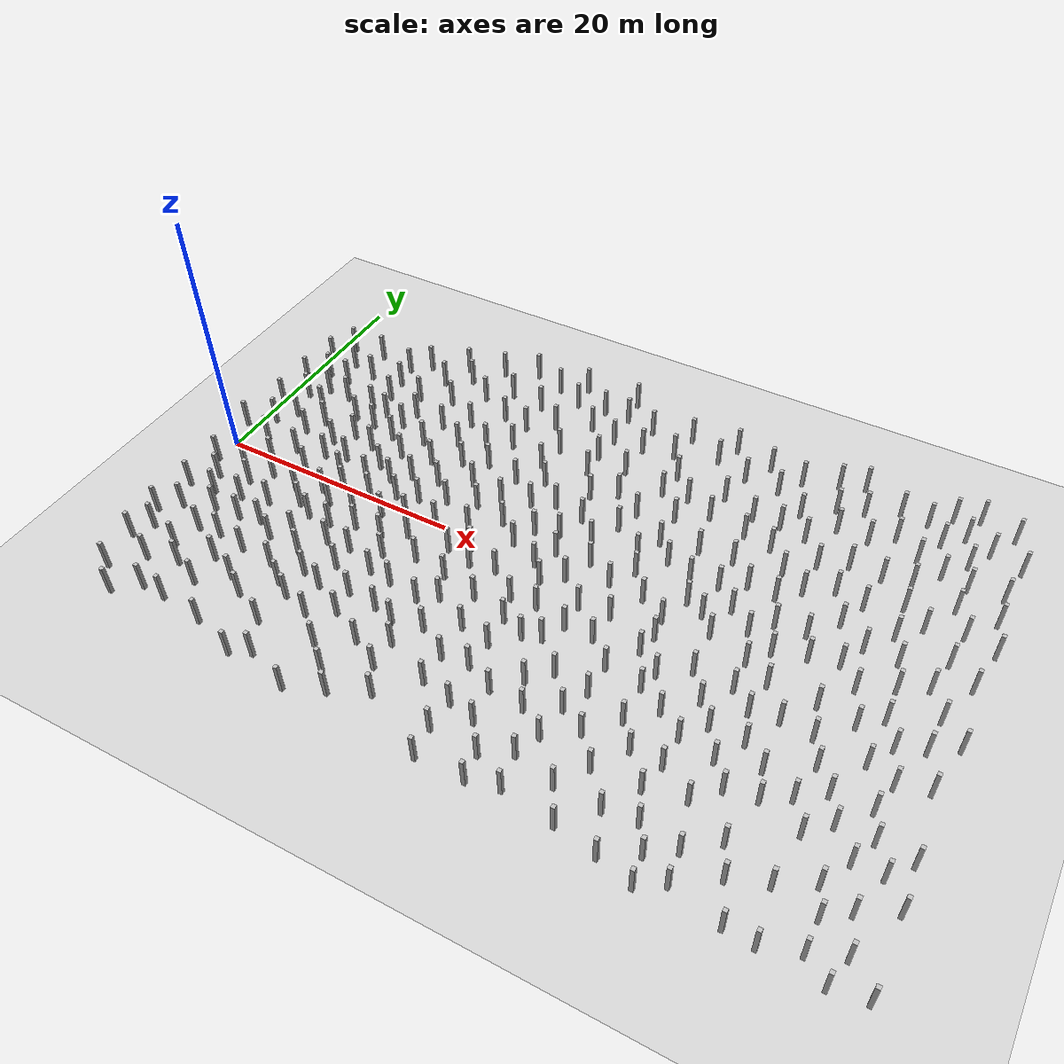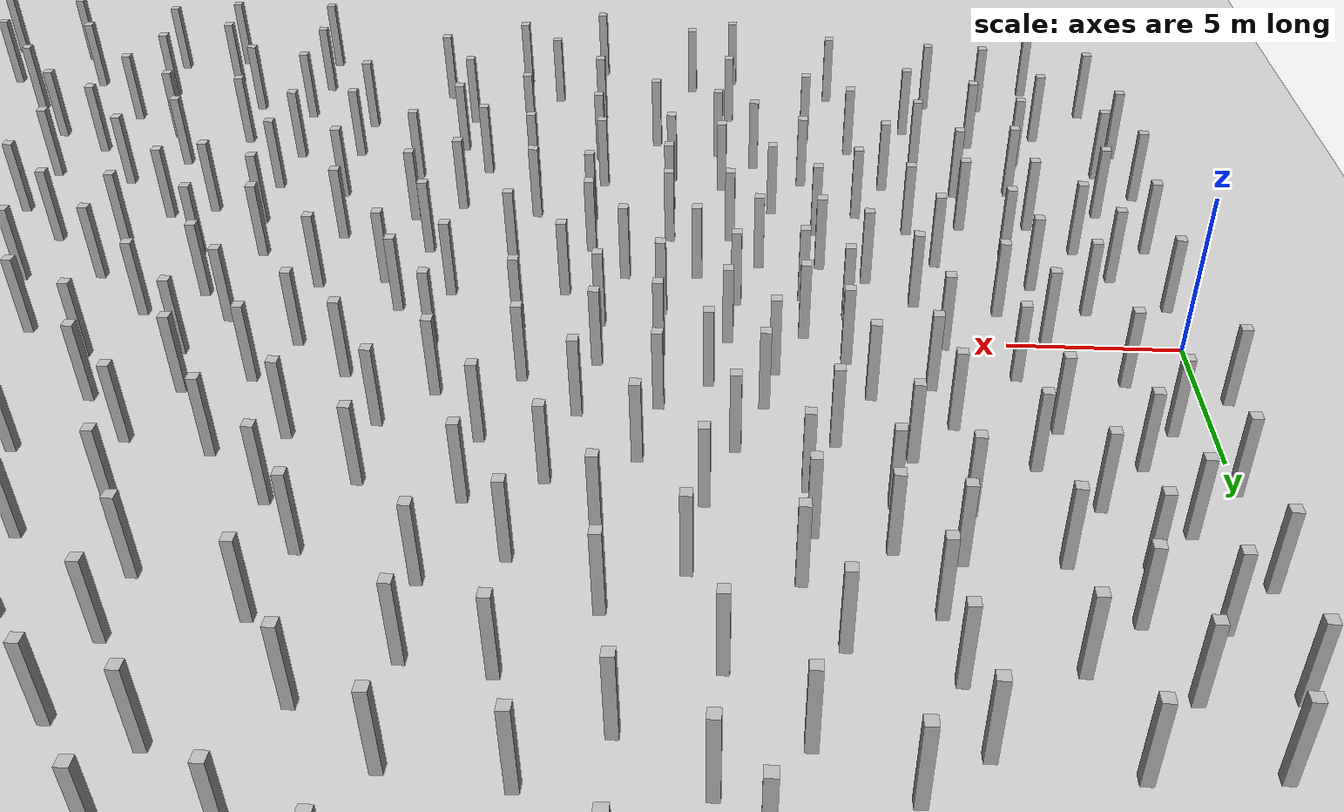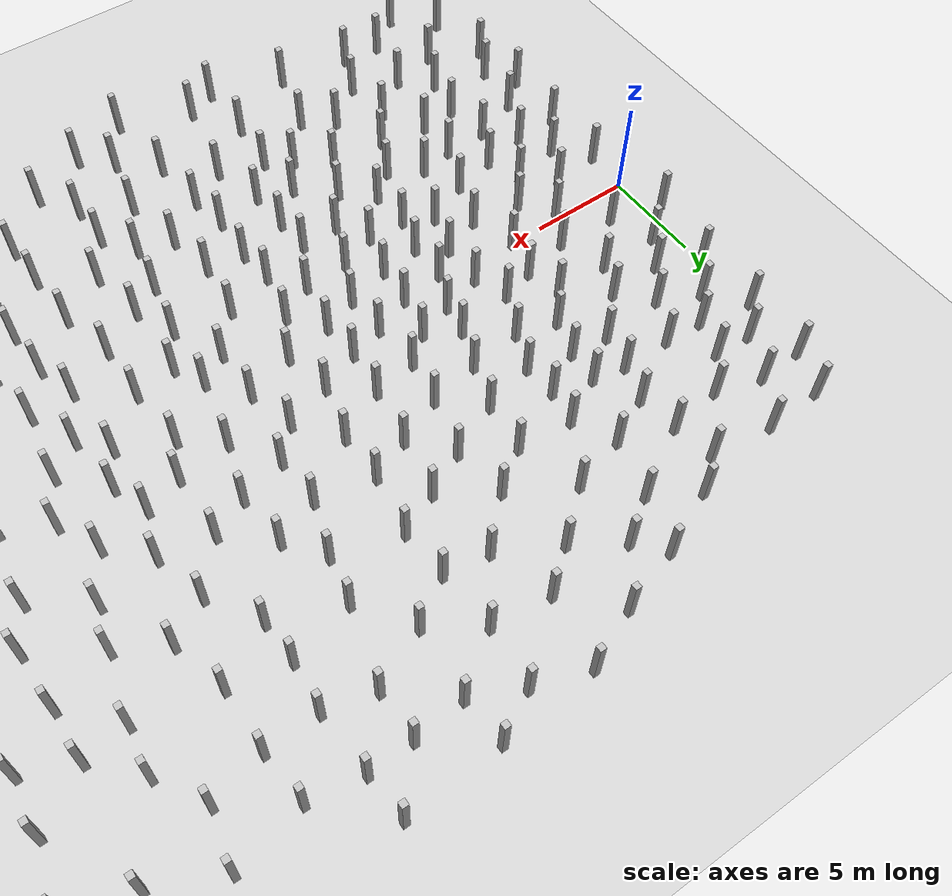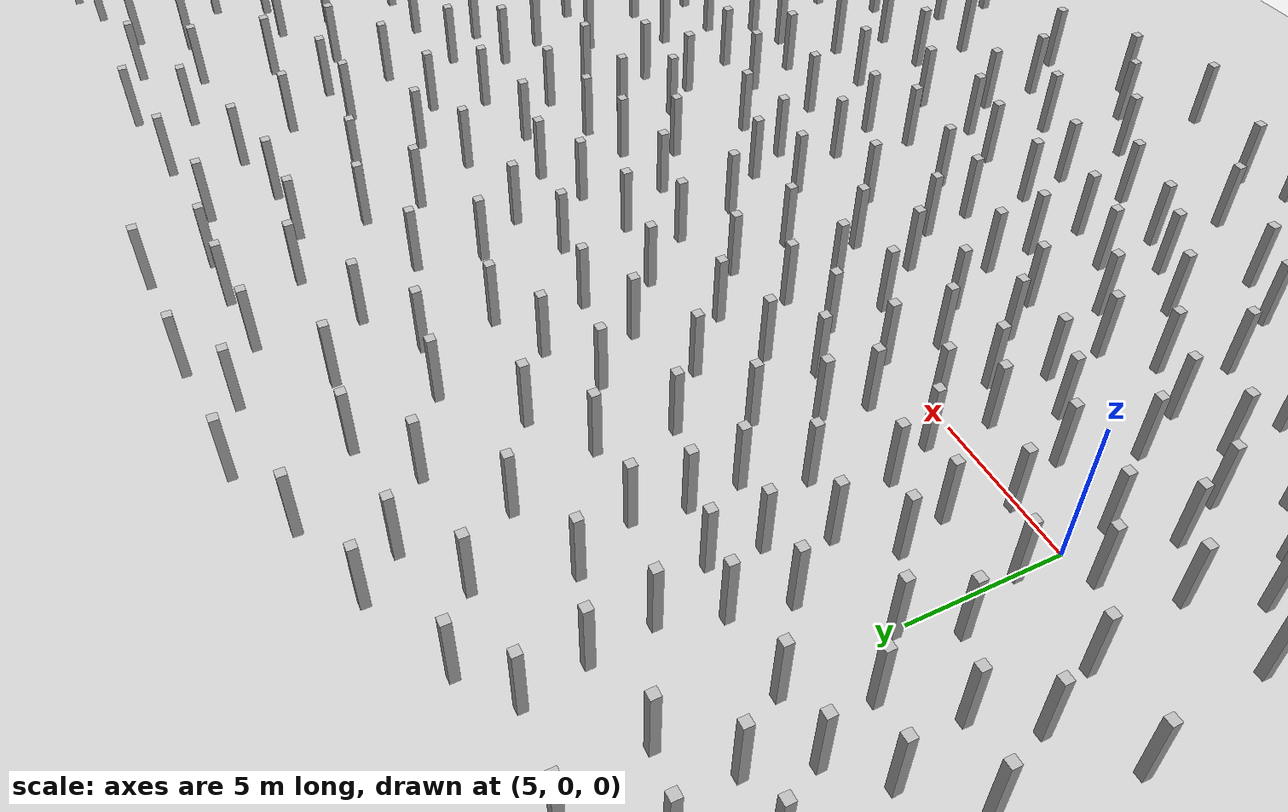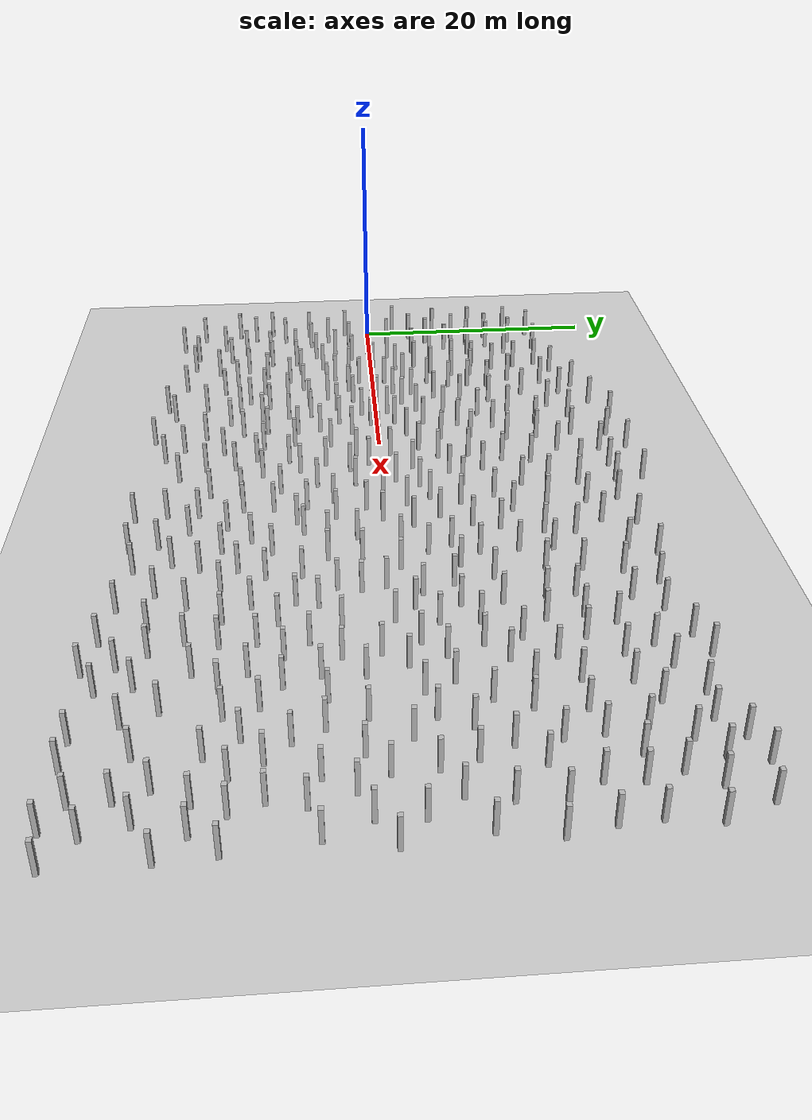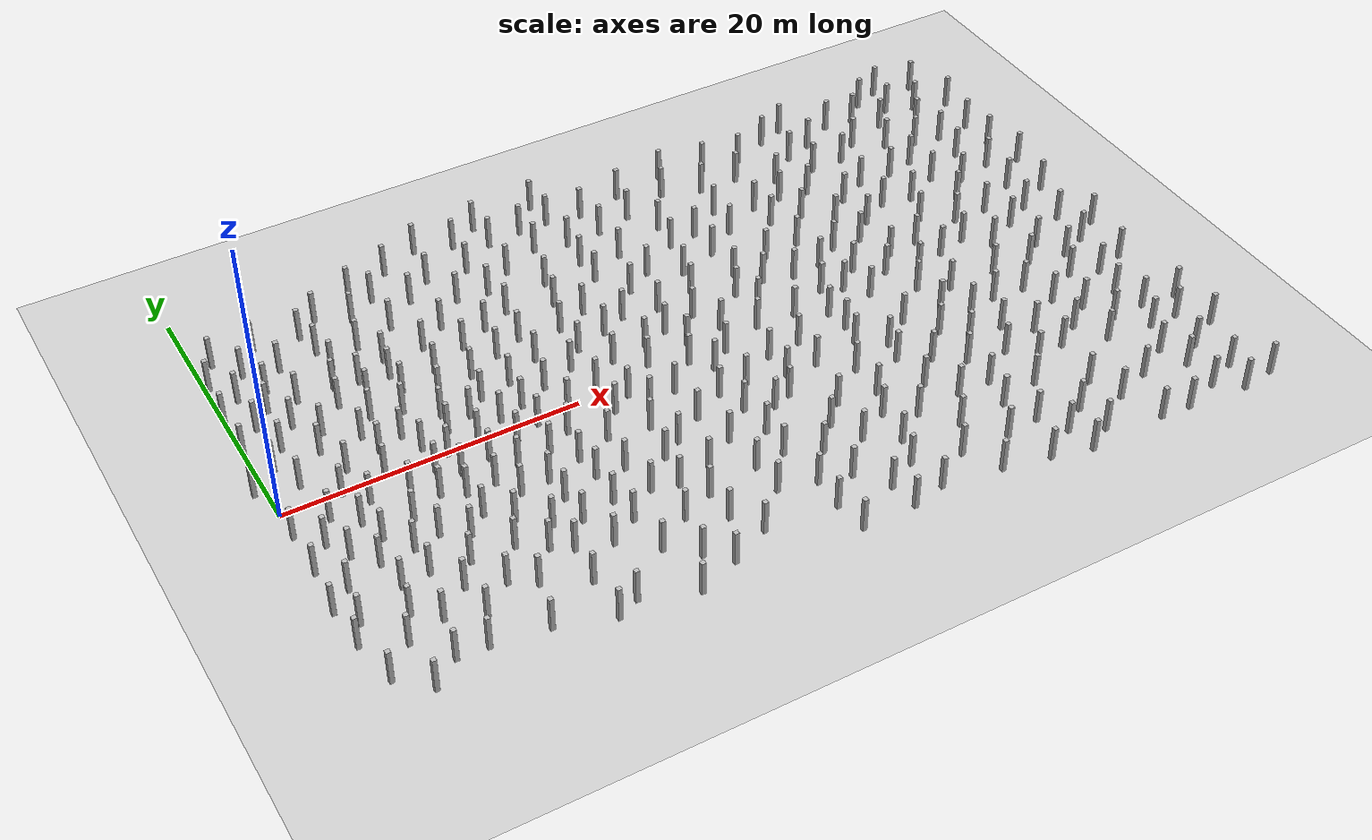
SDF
<sdf version="1.7">
 <world name="random_boxes_100x40_600">
  <light name="sun" type="directional">
   <pose>0 0 10 0 -0 0</pose>
   <diffuse>0.8 0.8 0.8 1</diffuse>
   <specular>0.2 0.2 0.2 1</specular>
   <attenuation>
    <range>1000</range>
    <constant>0.9</constant>
    <linear>0.01</linear>
    <quadratic>0.001</quadratic>
   </attenuation>
   <direction>-0.5 0.1 -0.9</direction>
   <spot><inner_angle>0</inner_angle><outer_angle>0</outer_angle><falloff>0</falloff></spot>
  </light>
  <model name="ground_plane">
   <static>1</static>
   <link name="link">
    <collision name="collision">
     <geometry><plane><normal>0 0 1</normal><size>100 100</size></plane></geometry>
     <surface><friction><ode><mu>100</mu><mu2>50</mu2></ode></friction></surface>
    </collision>
    <visual name="visual">
     <cast_shadows>0</cast_shadows>
     <geometry><plane><normal>0 0 1</normal><size>100 100</size></plane></geometry>
     <material>
      <script><uri>file://media/materials/scripts/gazebo.material</uri><name>Gazebo/Grey</name></script>
     </material>
    </visual>
   </link>
  </model>
  <model name="box_0">
   <static>1</static>
   <pose>17.4836 6.59513 1.25 0 -0 0</pose>
   <link name="link">
    <visual name="visual"><geometry><box><size>0.3 0.3 2.5</size></box></geometry></visual>
    <collision name="collision"><geometry><box><size>0.3 0.3 2.5</size></box></geometry></collision>
   </link>
  </model>
  <model name="box_1">
   <static>1</static>
   <pose>23.067 9.463 1.25 0 -0 0</pose>
   <link name="link">
    <visual name="visual"><geometry><box><size>0.3 0.3 2.5</size></box></geometry></visual>
    <collision name="collision"><geometry><box><size>0.3 0.3 2.5</size></box></geometry></collision>
   </link>
  </model>
  <model name="box_2">
   <static>1</static>
   <pose>15.2072 5.61376 1.25 0 -0 0</pose>
   <link name="link">
    <visual name="visual"><geometry><box><size>0.3 0.3 2.5</size></box></geometry></visual>
    <collision name="collision"><geometry><box><size>0.3 0.3 2.5</size></box></geometry></collision>
   </link>
  </model>
  <model name="box_3">
   <static>1</static>
   <pose>19.4562 5.02635 1.25 0 -0 0</pose>
   <link name="link">
    <visual name="visual"><geometry><box><size>0.3 0.3 2.5</size></box></geometry></visual>
    <collision name="collision"><geometry><box><size>0.3 0.3 2.5</size></box></geometry></collision>
   </link>
  </model>
  <model name="box_4">
   <static>1</static>
   <pose>19.4371 7.41929 1.25 0 -0 0</pose>
   <link name="link">
    <visual name="visual"><geometry><box><size>0.3 0.3 2.5</size></box></geometry></visual>
    <collision name="collision"><geometry><box><size>0.3 0.3 2.5</size></box></geometry></collision>
   </link>
  </model>
  <model name="box_5">
   <static>1</static>
   <pose>24.3431 7.76554 1.25 0 -0 0</pose>
   <link name="link">
    <visual name="visual"><geometry><box><size>0.3 0.3 2.5</size></box></geometry></visual>
    <collision name="collision"><geometry><box><size>0.3 0.3 2.5</size></box></geometry></collision>
   </link>
  </model>
  <model name="box_6">
   <static>1</static>
   <pose>15.948 8.4165 1.25 0 -0 0</pose>
   <link name="link">
    <visual name="visual"><geometry><box><size>0.3 0.3 2.5</size></box></geometry></visual>
    <collision name="collision"><geometry><box><size>0.3 0.3 2.5</size></box></geometry></collision>
   </link>
  </model>
  <model name="box_7">
   <static>1</static>
   <pose>23.516 11.668 1.25 0 -0 0</pose>
   <link name="link">
    <visual name="visual"><geometry><box><size>0.3 0.3 2.5</size></box></geometry></visual>
    <collision name="collision"><geometry><box><size>0.3 0.3 2.5</size></box></geometry></collision>
   </link>
  </model>
  <model name="box_8">
   <static>1</static>
   <pose>26.659 10.443 1.25 0 -0 0</pose>
   <link name="link">
    <visual name="visual"><geometry><box><size>0.3 0.3 2.5</size></box></geometry></visual>
    <collision name="collision"><geometry><box><size>0.3 0.3 2.5</size></box></geometry></collision>
   </link>
  </model>
  <model name="box_9">
   <static>1</static>
   <pose>17.9796 9.42606 1.25 0 -0 0</pose>
   <link name="link">
    <visual name="visual"><geometry><box><size>0.3 0.3 2.5</size></box></geometry></visual>
    <collision name="collision"><geometry><box><size>0.3 0.3 2.5</size></box></geometry></collision>
   </link>
  </model>
  <model name="box_10">
   <static>1</static>
   <pose>17.0221 3.80163 1.25 0 -0 0</pose>
   <link name="link">
    <visual name="visual"><geometry><box><size>0.3 0.3 2.5</size></box></geometry></visual>
    <collision name="collision"><geometry><box><size>0.3 0.3 2.5</size></box></geometry></collision>
   </link>
  </model>
  <model name="box_11">
   <static>1</static>
   <pose>22.2258 6.90257 1.25 0 -0 0</pose>
   <link name="link">
    <visual name="visual"><geometry><box><size>0.3 0.3 2.5</size></box></geometry></visual>
    <collision name="collision"><geometry><box><size>0.3 0.3 2.5</size></box></geometry></collision>
   </link>
  </model>
  <model name="box_12">
   <static>1</static>
   <pose>21.83 14.069 1.25 0 -0 0</pose>
   <link name="link">
    <visual name="visual"><geometry><box><size>0.3 0.3 2.5</size></box></geometry></visual>
    <collision name="collision"><geometry><box><size>0.3 0.3 2.5</size></box></geometry></collision>
   </link>
  </model>
  <model name="box_13">
   <static>1</static>
   <pose>13.3817 7.23787 1.25 0 -0 0</pose>
   <link name="link">
    <visual name="visual"><geometry><box><size>0.3 0.3 2.5</size></box></geometry></visual>
    <collision name="collision"><geometry><box><size>0.3 0.3 2.5</size></box></geometry></collision>
   </link>
  </model>
  <model name="box_14">
   <static>1</static>
   <pose>19.557 15.617 1.25 0 -0 0</pose>
   <link name="link">
    <visual name="visual"><geometry><box><size>0.3 0.3 2.5</size></box></geometry></visual>
    <collision name="collision"><geometry><box><size>0.3 0.3 2.5</size></box></geometry></collision>
   </link>
  </model>
  <model name="box_15">
   <static>1</static>
   <pose>14.8376 3.37622 1.25 0 -0 0</pose>
   <link name="link">
    <visual name="visual"><geometry><box><size>0.3 0.3 2.5</size></box></geometry></visual>
    <collision name="collision"><geometry><box><size>0.3 0.3 2.5</size></box></geometry></collision>
   </link>
  </model>
  <model name="box_16">
   <static>1</static>
   <pose>15.5586 11.012 1.25 0 -0 0</pose>
   <link name="link">
    <visual name="visual"><geometry><box><size>0.3 0.3 2.5</size></box></geometry></visual>
    <collision name="collision"><geometry><box><size>0.3 0.3 2.5</size></box></geometry></collision>
   </link>
  </model>
  <model name="box_17">
   <static>1</static>
   <pose>28.119 8.132 1.25 0 -0 0</pose>
   <link name="link">
    <visual name="visual"><geometry><box><size>0.3 0.3 2.5</size></box></geometry></visual>
    <collision name="collision"><geometry><box><size>0.3 0.3 2.5</size></box></geometry></collision>
   </link>
  </model>
  <model name="box_18">
   <static>1</static>
   <pose>21.0305 3.09446 1.25 0 -0 0</pose>
   <link name="link">
    <visual name="visual"><geometry><box><size>0.3 0.3 2.5</size></box></geometry></visual>
    <collision name="collision"><geometry><box><size>0.3 0.3 2.5</size></box></geometry></collision>
   </link>
  </model>
  <model name="box_19">
   <static>1</static>
   <pose>19.852 18.463 1.25 0 -0 0</pose>
   <link name="link">
    <visual name="visual"><geometry><box><size>0.3 0.3 2.5</size></box></geometry></visual>
    <collision name="collision"><geometry><box><size>0.3 0.3 2.5</size></box></geometry></collision>
   </link>
  </model>
  <model name="box_20">
   <static>1</static>
   <pose>19.9423 10.3127 1.25 0 -0 0</pose>
   <link name="link">
    <visual name="visual"><geometry><box><size>0.3 0.3 2.5</size></box></geometry></visual>
    <collision name="collision"><geometry><box><size>0.3 0.3 2.5</size></box></geometry></collision>
   </link>
  </model>
  <model name="box_21">
   <static>1</static>
   <pose>24.533 15.338 1.25 0 -0 0</pose>
   <link name="link">
    <visual name="visual"><geometry><box><size>0.3 0.3 2.5</size></box></geometry></visual>
    <collision name="collision"><geometry><box><size>0.3 0.3 2.5</size></box></geometry></collision>
   </link>
  </model>
  <model name="box_22">
   <static>1</static>
   <pose>26.589 12.455 1.25 0 -0 0</pose>
   <link name="link">
    <visual name="visual"><geometry><box><size>0.3 0.3 2.5</size></box></geometry></visual>
    <collision name="collision"><geometry><box><size>0.3 0.3 2.5</size></box></geometry></collision>
   </link>
  </model>
  <model name="box_23">
   <static>1</static>
   <pose>16.73 15.923 1.25 0 -0 0</pose>
   <link name="link">
    <visual name="visual"><geometry><box><size>0.3 0.3 2.5</size></box></geometry></visual>
    <collision name="collision"><geometry><box><size>0.3 0.3 2.5</size></box></geometry></collision>
   </link>
  </model>
  <model name="box_24">
   <static>1</static>
   <pose>26.821 14.765 1.25 0 -0 0</pose>
   <link name="link">
    <visual name="visual"><geometry><box><size>0.3 0.3 2.5</size></box></geometry></visual>
    <collision name="collision"><geometry><box><size>0.3 0.3 2.5</size></box></geometry></collision>
   </link>
  </model>
  <model name="box_25">
   <static>1</static>
   <pose>11.9703 3.1948 1.25 0 -0 0</pose>
   <link name="link">
    <visual name="visual"><geometry><box><size>0.3 0.3 2.5</size></box></geometry></visual>
    <collision name="collision"><geometry><box><size>0.3 0.3 2.5</size></box></geometry></collision>
   </link>
  </model>
  <model name="box_26">
   <static>1</static>
   <pose>13.6562 9.66763 1.25 0 -0 0</pose>
   <link name="link">
    <visual name="visual"><geometry><box><size>0.3 0.3 2.5</size></box></geometry></visual>
    <collision name="collision"><geometry><box><size>0.3 0.3 2.5</size></box></geometry></collision>
   </link>
  </model>
  <model name="box_27">
   <static>1</static>
   <pose>17.293 19.288 1.25 0 -0 0</pose>
   <link name="link">
    <visual name="visual"><geometry><box><size>0.3 0.3 2.5</size></box></geometry></visual>
    <collision name="collision"><geometry><box><size>0.3 0.3 2.5</size></box></geometry></collision>
   </link>
  </model>
  <model name="box_28">
   <static>1</static>
   <pose>9.04471 2.67448 1.25 0 -0 0</pose>
   <link name="link">
    <visual name="visual"><geometry><box><size>0.3 0.3 2.5</size></box></geometry></visual>
    <collision name="collision"><geometry><box><size>0.3 0.3 2.5</size></box></geometry></collision>
   </link>
  </model>
  <model name="box_29">
   <static>1</static>
   <pose>14.891 14.481 1.25 0 -0 0</pose>
   <link name="link">
    <visual name="visual"><geometry><box><size>0.3 0.3 2.5</size></box></geometry></visual>
    <collision name="collision"><geometry><box><size>0.3 0.3 2.5</size></box></geometry></collision>
   </link>
  </model>
  <model name="box_30">
   <static>1</static>
   <pose>12.6881 5.0803 1.25 0 -0 0</pose>
   <link name="link">
    <visual name="visual"><geometry><box><size>0.3 0.3 2.5</size></box></geometry></visual>
    <collision name="collision"><geometry><box><size>0.3 0.3 2.5</size></box></geometry></collision>
   </link>
  </model>
  <model name="box_31">
   <static>1</static>
   <pose>29.321 14.858 1.25 0 -0 0</pose>
   <link name="link">
    <visual name="visual"><geometry><box><size>0.3 0.3 2.5</size></box></geometry></visual>
    <collision name="collision"><geometry><box><size>0.3 0.3 2.5</size></box></geometry></collision>
   </link>
  </model>
  <model name="box_32">
   <static>1</static>
   <pose>22.106 17.415 1.25 0 -0 0</pose>
   <link name="link">
    <visual name="visual"><geometry><box><size>0.3 0.3 2.5</size></box></geometry></visual>
    <collision name="collision"><geometry><box><size>0.3 0.3 2.5</size></box></geometry></collision>
   </link>
  </model>
  <model name="box_33">
   <static>1</static>
   <pose>9.686 1.023 1.25 0 -0 0</pose>
   <link name="link">
    <visual name="visual"><geometry><box><size>0.3 0.3 2.5</size></box></geometry></visual>
    <collision name="collision"><geometry><box><size>0.3 0.3 2.5</size></box></geometry></collision>
   </link>
  </model>
  <model name="box_34">
   <static>1</static>
   <pose>7.356 2.145 1.25 0 -0 0</pose>
   <link name="link">
    <visual name="visual"><geometry><box><size>0.3 0.3 2.5</size></box></geometry></visual>
    <collision name="collision"><geometry><box><size>0.3 0.3 2.5</size></box></geometry></collision>
   </link>
  </model>
  <model name="box_35">
   <static>1</static>
   <pose>10.6857 8.21715 1.25 0 -0 0</pose>
   <link name="link">
    <visual name="visual"><geometry><box><size>0.3 0.3 2.5</size></box></geometry></visual>
    <collision name="collision"><geometry><box><size>0.3 0.3 2.5</size></box></geometry></collision>
   </link>
  </model>
  <model name="box_36">
   <static>1</static>
   <pose>21.923 19.605 1.25 0 -0 0</pose>
   <link name="link">
    <visual name="visual"><geometry><box><size>0.3 0.3 2.5</size></box></geometry></visual>
    <collision name="collision"><geometry><box><size>0.3 0.3 2.5</size></box></geometry></collision>
   </link>
  </model>
  <model name="box_37">
   <static>1</static>
   <pose>4.947 1.573 1.25 0 -0 0</pose>
   <link name="link">
    <visual name="visual"><geometry><box><size>0.3 0.3 2.5</size></box></geometry></visual>
    <collision name="collision"><geometry><box><size>0.3 0.3 2.5</size></box></geometry></collision>
   </link>
  </model>
  <model name="box_38">
   <static>1</static>
   <pose>31.835 15.458 1.25 0 -0 0</pose>
   <link name="link">
    <visual name="visual"><geometry><box><size>0.3 0.3 2.5</size></box></geometry></visual>
    <collision name="collision"><geometry><box><size>0.3 0.3 2.5</size></box></geometry></collision>
   </link>
  </model>
  <model name="box_39">
   <static>1</static>
   <pose>21.644 0.784753 1.25 0 -0 0</pose>
   <link name="link">
    <visual name="visual"><geometry><box><size>0.3 0.3 2.5</size></box></geometry></visual>
    <collision name="collision"><geometry><box><size>0.3 0.3 2.5</size></box></geometry></collision>
   </link>
  </model>
  <model name="box_40">
   <static>1</static>
   <pose>32.335 17.937 1.25 0 -0 0</pose>
   <link name="link">
    <visual name="visual"><geometry><box><size>0.3 0.3 2.5</size></box></geometry></visual>
    <collision name="collision"><geometry><box><size>0.3 0.3 2.5</size></box></geometry></collision>
   </link>
  </model>
  <model name="box_41">
   <static>1</static>
   <pose>9.607 -1.17 1.25 0 -0 0</pose>
   <link name="link">
    <visual name="visual"><geometry><box><size>0.3 0.3 2.5</size></box></geometry></visual>
    <collision name="collision"><geometry><box><size>0.3 0.3 2.5</size></box></geometry></collision>
   </link>
  </model>
  <model name="box_42">
   <static>1</static>
   <pose>21.5977 -1.87838 1.25 0 -0 0</pose>
   <link name="link">
    <visual name="visual"><geometry><box><size>0.3 0.3 2.5</size></box></geometry></visual>
    <collision name="collision"><geometry><box><size>0.3 0.3 2.5</size></box></geometry></collision>
   </link>
  </model>
  <model name="box_43">
   <static>1</static>
   <pose>8.98318 -3.23147 1.25 0 -0 0</pose>
   <link name="link">
    <visual name="visual"><geometry><box><size>0.3 0.3 2.5</size></box></geometry></visual>
    <collision name="collision"><geometry><box><size>0.3 0.3 2.5</size></box></geometry></collision>
   </link>
  </model>
  <model name="box_44">
   <static>1</static>
   <pose>9.17179 -7.16814 1.25 0 -0 0</pose>
   <link name="link">
    <visual name="visual"><geometry><box><size>0.3 0.3 2.5</size></box></geometry></visual>
    <collision name="collision"><geometry><box><size>0.3 0.3 2.5</size></box></geometry></collision>
   </link>
  </model>
  <model name="box_45">
   <static>1</static>
   <pose>17.6378 13.02 1.25 0 -0 0</pose>
   <link name="link">
    <visual name="visual"><geometry><box><size>0.3 0.3 2.5</size></box></geometry></visual>
    <collision name="collision"><geometry><box><size>0.3 0.3 2.5</size></box></geometry></collision>
   </link>
  </model>
  <model name="box_46">
   <static>1</static>
   <pose>29.089 17.269 1.25 0 -0 0</pose>
   <link name="link">
    <visual name="visual"><geometry><box><size>0.3 0.3 2.5</size></box></geometry></visual>
    <collision name="collision"><geometry><box><size>0.3 0.3 2.5</size></box></geometry></collision>
   </link>
  </model>
  <model name="box_47">
   <static>1</static>
   <pose>12.6696 12.6326 1.25 0 -0 0</pose>
   <link name="link">
    <visual name="visual"><geometry><box><size>0.3 0.3 2.5</size></box></geometry></visual>
    <collision name="collision"><geometry><box><size>0.3 0.3 2.5</size></box></geometry></collision>
   </link>
  </model>
  <model name="box_48">
   <static>1</static>
   <pose>6.85599 0.180495 1.25 0 -0 0</pose>
   <link name="link">
    <visual name="visual"><geometry><box><size>0.3 0.3 2.5</size></box></geometry></visual>
    <collision name="collision"><geometry><box><size>0.3 0.3 2.5</size></box></geometry></collision>
   </link>
  </model>
  <model name="box_49">
   <static>1</static>
   <pose>22.3143 4.50887 1.25 0 -0 0</pose>
   <link name="link">
    <visual name="visual"><geometry><box><size>0.3 0.3 2.5</size></box></geometry></visual>
    <collision name="collision"><geometry><box><size>0.3 0.3 2.5</size></box></geometry></collision>
   </link>
  </model>
  <model name="box_50">
   <static>1</static>
   <pose>19.23 -0.019738 1.25 0 -0 0</pose>
   <link name="link">
    <visual name="visual"><geometry><box><size>0.3 0.3 2.5</size></box></geometry></visual>
    <collision name="collision"><geometry><box><size>0.3 0.3 2.5</size></box></geometry></collision>
   </link>
  </model>
  <model name="box_51">
   <static>1</static>
   <pose>15.1182 -1.18065 1.25 0 -0 0</pose>
   <link name="link">
    <visual name="visual"><geometry><box><size>0.3 0.3 2.5</size></box></geometry></visual>
    <collision name="collision"><geometry><box><size>0.3 0.3 2.5</size></box></geometry></collision>
   </link>
  </model>
  <model name="box_52">
   <static>1</static>
   <pose>14.612 18.134 1.25 0 -0 0</pose>
   <link name="link">
    <visual name="visual"><geometry><box><size>0.3 0.3 2.5</size></box></geometry></visual>
    <collision name="collision"><geometry><box><size>0.3 0.3 2.5</size></box></geometry></collision>
   </link>
  </model>
  <model name="box_53">
   <static>1</static>
   <pose>33.13 13.301 1.25 0 -0 0</pose>
   <link name="link">
    <visual name="visual"><geometry><box><size>0.3 0.3 2.5</size></box></geometry></visual>
    <collision name="collision"><geometry><box><size>0.3 0.3 2.5</size></box></geometry></collision>
   </link>
  </model>
  <model name="box_54">
   <static>1</static>
   <pose>29.284 11.9067 1.25 0 -0 0</pose>
   <link name="link">
    <visual name="visual"><geometry><box><size>0.3 0.3 2.5</size></box></geometry></visual>
    <collision name="collision"><geometry><box><size>0.3 0.3 2.5</size></box></geometry></collision>
   </link>
  </model>
  <model name="box_55">
   <static>1</static>
   <pose>7.58574 -1.98708 1.25 0 -0 0</pose>
   <link name="link">
    <visual name="visual"><geometry><box><size>0.3 0.3 2.5</size></box></geometry></visual>
    <collision name="collision"><geometry><box><size>0.3 0.3 2.5</size></box></geometry></collision>
   </link>
  </model>
  <model name="box_56">
   <static>1</static>
   <pose>30.006 9.267 1.25 0 -0 0</pose>
   <link name="link">
    <visual name="visual"><geometry><box><size>0.3 0.3 2.5</size></box></geometry></visual>
    <collision name="collision"><geometry><box><size>0.3 0.3 2.5</size></box></geometry></collision>
   </link>
  </model>
  <model name="box_57">
   <static>1</static>
   <pose>8.77159 8.68753 1.25 0 -0 0</pose>
   <link name="link">
    <visual name="visual"><geometry><box><size>0.3 0.3 2.5</size></box></geometry></visual>
    <collision name="collision"><geometry><box><size>0.3 0.3 2.5</size></box></geometry></collision>
   </link>
  </model>
  <model name="box_58">
   <static>1</static>
   <pose>6.88706 3.84569 1.25 0 -0 0</pose>
   <link name="link">
    <visual name="visual"><geometry><box><size>0.3 0.3 2.5</size></box></geometry></visual>
    <collision name="collision"><geometry><box><size>0.3 0.3 2.5</size></box></geometry></collision>
   </link>
  </model>
  <model name="box_59">
   <static>1</static>
   <pose>13.5333 2.28479 1.25 0 -0 0</pose>
   <link name="link">
    <visual name="visual"><geometry><box><size>0.3 0.3 2.5</size></box></geometry></visual>
    <collision name="collision"><geometry><box><size>0.3 0.3 2.5</size></box></geometry></collision>
   </link>
  </model>
  <model name="box_60">
   <static>1</static>
   <pose>10.0602 4.73044 1.25 0 -0 0</pose>
   <link name="link">
    <visual name="visual"><geometry><box><size>0.3 0.3 2.5</size></box></geometry></visual>
    <collision name="collision"><geometry><box><size>0.3 0.3 2.5</size></box></geometry></collision>
   </link>
  </model>
  <model name="box_61">
   <static>1</static>
   <pose>11.6059 17.1727 1.25 0 -0 0</pose>
   <link name="link">
    <visual name="visual"><geometry><box><size>0.3 0.3 2.5</size></box></geometry></visual>
    <collision name="collision"><geometry><box><size>0.3 0.3 2.5</size></box></geometry></collision>
   </link>
  </model>
  <model name="box_62">
   <static>1</static>
   <pose>10.9113 -2.13782 1.25 0 -0 0</pose>
   <link name="link">
    <visual name="visual"><geometry><box><size>0.3 0.3 2.5</size></box></geometry></visual>
    <collision name="collision"><geometry><box><size>0.3 0.3 2.5</size></box></geometry></collision>
   </link>
  </model>
  <model name="box_63">
   <static>1</static>
   <pose>12.2999 -3.95113 1.25 0 -0 0</pose>
   <link name="link">
    <visual name="visual"><geometry><box><size>0.3 0.3 2.5</size></box></geometry></visual>
    <collision name="collision"><geometry><box><size>0.3 0.3 2.5</size></box></geometry></collision>
   </link>
  </model>
  <model name="box_64">
   <static>1</static>
   <pose>10.4993 -6.00847 1.25 0 -0 0</pose>
   <link name="link">
    <visual name="visual"><geometry><box><size>0.3 0.3 2.5</size></box></geometry></visual>
    <collision name="collision"><geometry><box><size>0.3 0.3 2.5</size></box></geometry></collision>
   </link>
  </model>
  <model name="box_65">
   <static>1</static>
   <pose>12.9216 -1.81684 1.25 0 -0 0</pose>
   <link name="link">
    <visual name="visual"><geometry><box><size>0.3 0.3 2.5</size></box></geometry></visual>
    <collision name="collision"><geometry><box><size>0.3 0.3 2.5</size></box></geometry></collision>
   </link>
  </model>
  <model name="box_66">
   <static>1</static>
   <pose>1.96698 1.6933 1.25 0 -0 0</pose>
   <link name="link">
    <visual name="visual"><geometry><box><size>0.3 0.3 2.5</size></box></geometry></visual>
    <collision name="collision"><geometry><box><size>0.3 0.3 2.5</size></box></geometry></collision>
   </link>
  </model>
  <model name="box_67">
   <static>1</static>
   <pose>12.713 15.901 1.25 0 -0 0</pose>
   <link name="link">
    <visual name="visual"><geometry><box><size>0.3 0.3 2.5</size></box></geometry></visual>
    <collision name="collision"><geometry><box><size>0.3 0.3 2.5</size></box></geometry></collision>
   </link>
  </model>
  <model name="box_68">
   <static>1</static>
   <pose>8.65293 7.04466 1.25 0 -0 0</pose>
   <link name="link">
    <visual name="visual"><geometry><box><size>0.3 0.3 2.5</size></box></geometry></visual>
    <collision name="collision"><geometry><box><size>0.3 0.3 2.5</size></box></geometry></collision>
   </link>
  </model>
  <model name="box_69">
   <static>1</static>
   <pose>32.147 8.051 1.25 0 -0 0</pose>
   <link name="link">
    <visual name="visual"><geometry><box><size>0.3 0.3 2.5</size></box></geometry></visual>
    <collision name="collision"><geometry><box><size>0.3 0.3 2.5</size></box></geometry></collision>
   </link>
  </model>
  <model name="box_70">
   <static>1</static>
   <pose>8.61097 15.8419 1.25 0 -0 0</pose>
   <link name="link">
    <visual name="visual"><geometry><box><size>0.3 0.3 2.5</size></box></geometry></visual>
    <collision name="collision"><geometry><box><size>0.3 0.3 2.5</size></box></geometry></collision>
   </link>
  </model>
  <model name="box_71">
   <static>1</static>
   <pose>7.55234 -6.21545 1.25 0 -0 0</pose>
   <link name="link">
    <visual name="visual"><geometry><box><size>0.3 0.3 2.5</size></box></geometry></visual>
    <collision name="collision"><geometry><box><size>0.3 0.3 2.5</size></box></geometry></collision>
   </link>
  </model>
  <model name="box_72">
   <static>1</static>
   <pose>4.03977 15.0454 1.25 0 -0 0</pose>
   <link name="link">
    <visual name="visual"><geometry><box><size>0.3 0.3 2.5</size></box></geometry></visual>
    <collision name="collision"><geometry><box><size>0.3 0.3 2.5</size></box></geometry></collision>
   </link>
  </model>
  <model name="box_73">
   <static>1</static>
   <pose>34.911 11.383 1.25 0 -0 0</pose>
   <link name="link">
    <visual name="visual"><geometry><box><size>0.3 0.3 2.5</size></box></geometry></visual>
    <collision name="collision"><geometry><box><size>0.3 0.3 2.5</size></box></geometry></collision>
   </link>
  </model>
  <model name="box_74">
   <static>1</static>
   <pose>8.07681 5.24452 1.25 0 -0 0</pose>
   <link name="link">
    <visual name="visual"><geometry><box><size>0.3 0.3 2.5</size></box></geometry></visual>
    <collision name="collision"><geometry><box><size>0.3 0.3 2.5</size></box></geometry></collision>
   </link>
  </model>
  <model name="box_75">
   <static>1</static>
   <pose>4.92264 5.42633 1.25 0 -0 0</pose>
   <link name="link">
    <visual name="visual"><geometry><box><size>0.3 0.3 2.5</size></box></geometry></visual>
    <collision name="collision"><geometry><box><size>0.3 0.3 2.5</size></box></geometry></collision>
   </link>
  </model>
  <model name="box_76">
   <static>1</static>
   <pose>13.0873 0.162636 1.25 0 -0 0</pose>
   <link name="link">
    <visual name="visual"><geometry><box><size>0.3 0.3 2.5</size></box></geometry></visual>
    <collision name="collision"><geometry><box><size>0.3 0.3 2.5</size></box></geometry></collision>
   </link>
  </model>
  <model name="box_77">
   <static>1</static>
   <pose>23.0122 -0.959011 1.25 0 -0 0</pose>
   <link name="link">
    <visual name="visual"><geometry><box><size>0.3 0.3 2.5</size></box></geometry></visual>
    <collision name="collision"><geometry><box><size>0.3 0.3 2.5</size></box></geometry></collision>
   </link>
  </model>
  <model name="box_78">
   <static>1</static>
   <pose>10.8915 -0.190176 1.25 0 -0 0</pose>
   <link name="link">
    <visual name="visual"><geometry><box><size>0.3 0.3 2.5</size></box></geometry></visual>
    <collision name="collision"><geometry><box><size>0.3 0.3 2.5</size></box></geometry></collision>
   </link>
  </model>
  <model name="box_79">
   <static>1</static>
   <pose>11.712 1.638 1.25 0 -0 0</pose>
   <link name="link">
    <visual name="visual"><geometry><box><size>0.3 0.3 2.5</size></box></geometry></visual>
    <collision name="collision"><geometry><box><size>0.3 0.3 2.5</size></box></geometry></collision>
   </link>
  </model>
  <model name="box_80">
   <static>1</static>
   <pose>4.14774 3.8578 1.25 0 -0 0</pose>
   <link name="link">
    <visual name="visual"><geometry><box><size>0.3 0.3 2.5</size></box></geometry></visual>
    <collision name="collision"><geometry><box><size>0.3 0.3 2.5</size></box></geometry></collision>
   </link>
  </model>
  <model name="box_81">
   <static>1</static>
   <pose>26.273 2.74732 1.25 0 -0 0</pose>
   <link name="link">
    <visual name="visual"><geometry><box><size>0.3 0.3 2.5</size></box></geometry></visual>
    <collision name="collision"><geometry><box><size>0.3 0.3 2.5</size></box></geometry></collision>
   </link>
  </model>
  <model name="box_82">
   <static>1</static>
   <pose>5.80402 -6.60036 1.25 0 -0 0</pose>
   <link name="link">
    <visual name="visual"><geometry><box><size>0.3 0.3 2.5</size></box></geometry></visual>
    <collision name="collision"><geometry><box><size>0.3 0.3 2.5</size></box></geometry></collision>
   </link>
  </model>
  <model name="box_83">
   <static>1</static>
   <pose>6.77163 -4.2783 1.25 0 -0 0</pose>
   <link name="link">
    <visual name="visual"><geometry><box><size>0.3 0.3 2.5</size></box></geometry></visual>
    <collision name="collision"><geometry><box><size>0.3 0.3 2.5</size></box></geometry></collision>
   </link>
  </model>
  <model name="box_84">
   <static>1</static>
   <pose>34.91 8.945 1.25 0 -0 0</pose>
   <link name="link">
    <visual name="visual"><geometry><box><size>0.3 0.3 2.5</size></box></geometry></visual>
    <collision name="collision"><geometry><box><size>0.3 0.3 2.5</size></box></geometry></collision>
   </link>
  </model>
  <model name="box_85">
   <static>1</static>
   <pose>7.1208 14.663 1.25 0 -0 0</pose>
   <link name="link">
    <visual name="visual"><geometry><box><size>0.3 0.3 2.5</size></box></geometry></visual>
    <collision name="collision"><geometry><box><size>0.3 0.3 2.5</size></box></geometry></collision>
   </link>
  </model>
  <model name="box_86">
   <static>1</static>
   <pose>5.78945 -8.75363 1.25 0 -0 0</pose>
   <link name="link">
    <visual name="visual"><geometry><box><size>0.3 0.3 2.5</size></box></geometry></visual>
    <collision name="collision"><geometry><box><size>0.3 0.3 2.5</size></box></geometry></collision>
   </link>
  </model>
  <model name="box_87">
   <static>1</static>
   <pose>11.9571 -7.32286 1.25 0 -0 0</pose>
   <link name="link">
    <visual name="visual"><geometry><box><size>0.3 0.3 2.5</size></box></geometry></visual>
    <collision name="collision"><geometry><box><size>0.3 0.3 2.5</size></box></geometry></collision>
   </link>
  </model>
  <model name="box_88">
   <static>1</static>
   <pose>15.323 -7.21574 1.25 0 -0 0</pose>
   <link name="link">
    <visual name="visual"><geometry><box><size>0.3 0.3 2.5</size></box></geometry></visual>
    <collision name="collision"><geometry><box><size>0.3 0.3 2.5</size></box></geometry></collision>
   </link>
  </model>
  <model name="box_89">
   <static>1</static>
   <pose>24.5668 5.16646 1.25 0 -0 0</pose>
   <link name="link">
    <visual name="visual"><geometry><box><size>0.3 0.3 2.5</size></box></geometry></visual>
    <collision name="collision"><geometry><box><size>0.3 0.3 2.5</size></box></geometry></collision>
   </link>
  </model>
  <model name="box_90">
   <static>1</static>
   <pose>32.875 11.088 1.25 0 -0 0</pose>
   <link name="link">
    <visual name="visual"><geometry><box><size>0.3 0.3 2.5</size></box></geometry></visual>
    <collision name="collision"><geometry><box><size>0.3 0.3 2.5</size></box></geometry></collision>
   </link>
  </model>
  <model name="box_91">
   <static>1</static>
   <pose>35.016 6.193 1.25 0 -0 0</pose>
   <link name="link">
    <visual name="visual"><geometry><box><size>0.3 0.3 2.5</size></box></geometry></visual>
    <collision name="collision"><geometry><box><size>0.3 0.3 2.5</size></box></geometry></collision>
   </link>
  </model>
  <model name="box_92">
   <static>1</static>
   <pose>10.9579 9.86808 1.25 0 -0 0</pose>
   <link name="link">
    <visual name="visual"><geometry><box><size>0.3 0.3 2.5</size></box></geometry></visual>
    <collision name="collision"><geometry><box><size>0.3 0.3 2.5</size></box></geometry></collision>
   </link>
  </model>
  <model name="box_93">
   <static>1</static>
   <pose>37.881 6.78 1.25 0 -0 0</pose>
   <link name="link">
    <visual name="visual"><geometry><box><size>0.3 0.3 2.5</size></box></geometry></visual>
    <collision name="collision"><geometry><box><size>0.3 0.3 2.5</size></box></geometry></collision>
   </link>
  </model>
  <model name="box_94">
   <static>1</static>
   <pose>26.3417 5.98152 1.25 0 -0 0</pose>
   <link name="link">
    <visual name="visual"><geometry><box><size>0.3 0.3 2.5</size></box></geometry></visual>
    <collision name="collision"><geometry><box><size>0.3 0.3 2.5</size></box></geometry></collision>
   </link>
  </model>
  <model name="box_95">
   <static>1</static>
   <pose>3.59462 -6.70837 1.25 0 -0 0</pose>
   <link name="link">
    <visual name="visual"><geometry><box><size>0.3 0.3 2.5</size></box></geometry></visual>
    <collision name="collision"><geometry><box><size>0.3 0.3 2.5</size></box></geometry></collision>
   </link>
  </model>
  <model name="box_96">
   <static>1</static>
   <pose>40.504 6.997 1.25 0 -0 0</pose>
   <link name="link">
    <visual name="visual"><geometry><box><size>0.3 0.3 2.5</size></box></geometry></visual>
    <collision name="collision"><geometry><box><size>0.3 0.3 2.5</size></box></geometry></collision>
   </link>
  </model>
  <model name="box_97">
   <static>1</static>
   <pose>23.7658 -2.44434 1.25 0 -0 0</pose>
   <link name="link">
    <visual name="visual"><geometry><box><size>0.3 0.3 2.5</size></box></geometry></visual>
    <collision name="collision"><geometry><box><size>0.3 0.3 2.5</size></box></geometry></collision>
   </link>
  </model>
  <model name="box_98">
   <static>1</static>
   <pose>4.97922 -12.4046 1.25 0 -0 0</pose>
   <link name="link">
    <visual name="visual"><geometry><box><size>0.3 0.3 2.5</size></box></geometry></visual>
    <collision name="collision"><geometry><box><size>0.3 0.3 2.5</size></box></geometry></collision>
   </link>
  </model>
  <model name="box_99">
   <static>1</static>
   <pose>7.15414 8.98177 1.25 0 -0 0</pose>
   <link name="link">
    <visual name="visual"><geometry><box><size>0.3 0.3 2.5</size></box></geometry></visual>
    <collision name="collision"><geometry><box><size>0.3 0.3 2.5</size></box></geometry></collision>
   </link>
  </model>
  <model name="box_100">
   <static>1</static>
   <pose>26.641 17.713 1.25 0 -0 0</pose>
   <link name="link">
    <visual name="visual"><geometry><box><size>0.3 0.3 2.5</size></box></geometry></visual>
    <collision name="collision"><geometry><box><size>0.3 0.3 2.5</size></box></geometry></collision>
   </link>
  </model>
  <model name="box_101">
   <static>1</static>
   <pose>2.54893 -13.0805 1.25 0 -0 0</pose>
   <link name="link">
    <visual name="visual"><geometry><box><size>0.3 0.3 2.5</size></box></geometry></visual>
    <collision name="collision"><geometry><box><size>0.3 0.3 2.5</size></box></geometry></collision>
   </link>
  </model>
  <model name="box_102">
   <static>1</static>
   <pose>25.4885 0.979209 1.25 0 -0 0</pose>
   <link name="link">
    <visual name="visual"><geometry><box><size>0.3 0.3 2.5</size></box></geometry></visual>
    <collision name="collision"><geometry><box><size>0.3 0.3 2.5</size></box></geometry></collision>
   </link>
  </model>
  <model name="box_103">
   <static>1</static>
   <pose>13.6799 -8.82067 1.25 0 -0 0</pose>
   <link name="link">
    <visual name="visual"><geometry><box><size>0.3 0.3 2.5</size></box></geometry></visual>
    <collision name="collision"><geometry><box><size>0.3 0.3 2.5</size></box></geometry></collision>
   </link>
  </model>
  <model name="box_104">
   <static>1</static>
   <pose>28.0736 3.34242 1.25 0 -0 0</pose>
   <link name="link">
    <visual name="visual"><geometry><box><size>0.3 0.3 2.5</size></box></geometry></visual>
    <collision name="collision"><geometry><box><size>0.3 0.3 2.5</size></box></geometry></collision>
   </link>
  </model>
  <model name="box_105">
   <static>1</static>
   <pose>0.772567 -10.341 1.25 0 -0 0</pose>
   <link name="link">
    <visual name="visual"><geometry><box><size>0.3 0.3 2.5</size></box></geometry></visual>
    <collision name="collision"><geometry><box><size>0.3 0.3 2.5</size></box></geometry></collision>
   </link>
  </model>
  <model name="box_106">
   <static>1</static>
   <pose>8.20837 -9.11857 1.25 0 -0 0</pose>
   <link name="link">
    <visual name="visual"><geometry><box><size>0.3 0.3 2.5</size></box></geometry></visual>
    <collision name="collision"><geometry><box><size>0.3 0.3 2.5</size></box></geometry></collision>
   </link>
  </model>
  <model name="box_107">
   <static>1</static>
   <pose>37.163 10.414 1.25 0 -0 0</pose>
   <link name="link">
    <visual name="visual"><geometry><box><size>0.3 0.3 2.5</size></box></geometry></visual>
    <collision name="collision"><geometry><box><size>0.3 0.3 2.5</size></box></geometry></collision>
   </link>
  </model>
  <model name="box_108">
   <static>1</static>
   <pose>-0.234938 -8.85022 1.25 0 -0 0</pose>
   <link name="link">
    <visual name="visual"><geometry><box><size>0.3 0.3 2.5</size></box></geometry></visual>
    <collision name="collision"><geometry><box><size>0.3 0.3 2.5</size></box></geometry></collision>
   </link>
  </model>
  <model name="box_109">
   <static>1</static>
   <pose>38.416 4.005 1.25 0 -0 0</pose>
   <link name="link">
    <visual name="visual"><geometry><box><size>0.3 0.3 2.5</size></box></geometry></visual>
    <collision name="collision"><geometry><box><size>0.3 0.3 2.5</size></box></geometry></collision>
   </link>
  </model>
  <model name="box_110">
   <static>1</static>
   <pose>7.75685 10.7393 1.25 0 -0 0</pose>
   <link name="link">
    <visual name="visual"><geometry><box><size>0.3 0.3 2.5</size></box></geometry></visual>
    <collision name="collision"><geometry><box><size>0.3 0.3 2.5</size></box></geometry></collision>
   </link>
  </model>
  <model name="box_111">
   <static>1</static>
   <pose>3.95259 -3.10227 1.25 0 -0 0</pose>
   <link name="link">
    <visual name="visual"><geometry><box><size>0.3 0.3 2.5</size></box></geometry></visual>
    <collision name="collision"><geometry><box><size>0.3 0.3 2.5</size></box></geometry></collision>
   </link>
  </model>
  <model name="box_112">
   <static>1</static>
   <pose>40.581 4.208 1.25 0 -0 0</pose>
   <link name="link">
    <visual name="visual"><geometry><box><size>0.3 0.3 2.5</size></box></geometry></visual>
    <collision name="collision"><geometry><box><size>0.3 0.3 2.5</size></box></geometry></collision>
   </link>
  </model>
  <model name="box_113">
   <static>1</static>
   <pose>27.8996 -0.118362 1.25 0 -0 0</pose>
   <link name="link">
    <visual name="visual"><geometry><box><size>0.3 0.3 2.5</size></box></geometry></visual>
    <collision name="collision"><geometry><box><size>0.3 0.3 2.5</size></box></geometry></collision>
   </link>
  </model>
  <model name="box_114">
   <static>1</static>
   <pose>7.49214 12.714 1.25 0 -0 0</pose>
   <link name="link">
    <visual name="visual"><geometry><box><size>0.3 0.3 2.5</size></box></geometry></visual>
    <collision name="collision"><geometry><box><size>0.3 0.3 2.5</size></box></geometry></collision>
   </link>
  </model>
  <model name="box_115">
   <static>1</static>
   <pose>14.1754 -3.22872 1.25 0 -0 0</pose>
   <link name="link">
    <visual name="visual"><geometry><box><size>0.3 0.3 2.5</size></box></geometry></visual>
    <collision name="collision"><geometry><box><size>0.3 0.3 2.5</size></box></geometry></collision>
   </link>
  </model>
  <model name="box_116">
   <static>1</static>
   <pose>10.9773 -9.29721 1.25 0 -0 0</pose>
   <link name="link">
    <visual name="visual"><geometry><box><size>0.3 0.3 2.5</size></box></geometry></visual>
    <collision name="collision"><geometry><box><size>0.3 0.3 2.5</size></box></geometry></collision>
   </link>
  </model>
  <model name="box_117">
   <static>1</static>
   <pose>4.55402 -4.83846 1.25 0 -0 0</pose>
   <link name="link">
    <visual name="visual"><geometry><box><size>0.3 0.3 2.5</size></box></geometry></visual>
    <collision name="collision"><geometry><box><size>0.3 0.3 2.5</size></box></geometry></collision>
   </link>
  </model>
  <model name="box_118">
   <static>1</static>
   <pose>30.4683 3.85748 1.25 0 -0 0</pose>
   <link name="link">
    <visual name="visual"><geometry><box><size>0.3 0.3 2.5</size></box></geometry></visual>
    <collision name="collision"><geometry><box><size>0.3 0.3 2.5</size></box></geometry></collision>
   </link>
  </model>
  <model name="box_119">
   <static>1</static>
   <pose>19.6916 -6.69948 1.25 0 -0 0</pose>
   <link name="link">
    <visual name="visual"><geometry><box><size>0.3 0.3 2.5</size></box></geometry></visual>
    <collision name="collision"><geometry><box><size>0.3 0.3 2.5</size></box></geometry></collision>
   </link>
  </model>
  <model name="box_120">
   <static>1</static>
   <pose>4.35086 -15.3913 1.25 0 -0 0</pose>
   <link name="link">
    <visual name="visual"><geometry><box><size>0.3 0.3 2.5</size></box></geometry></visual>
    <collision name="collision"><geometry><box><size>0.3 0.3 2.5</size></box></geometry></collision>
   </link>
  </model>
  <model name="box_121">
   <static>1</static>
   <pose>16.7444 1.4654 1.25 0 -0 0</pose>
   <link name="link">
    <visual name="visual"><geometry><box><size>0.3 0.3 2.5</size></box></geometry></visual>
    <collision name="collision"><geometry><box><size>0.3 0.3 2.5</size></box></geometry></collision>
   </link>
  </model>
  <model name="box_122">
   <static>1</static>
   <pose>5.12973 -1.6381 1.25 0 -0 0</pose>
   <link name="link">
    <visual name="visual"><geometry><box><size>0.3 0.3 2.5</size></box></geometry></visual>
    <collision name="collision"><geometry><box><size>0.3 0.3 2.5</size></box></geometry></collision>
   </link>
  </model>
  <model name="box_123">
   <static>1</static>
   <pose>16.3994 -3.09196 1.25 0 -0 0</pose>
   <link name="link">
    <visual name="visual"><geometry><box><size>0.3 0.3 2.5</size></box></geometry></visual>
    <collision name="collision"><geometry><box><size>0.3 0.3 2.5</size></box></geometry></collision>
   </link>
  </model>
  <model name="box_124">
   <static>1</static>
   <pose>33.573 0.771 1.25 0 -0 0</pose>
   <link name="link">
    <visual name="visual"><geometry><box><size>0.3 0.3 2.5</size></box></geometry></visual>
    <collision name="collision"><geometry><box><size>0.3 0.3 2.5</size></box></geometry></collision>
   </link>
  </model>
  <model name="box_125">
   <static>1</static>
   <pose>6.3342 -15.516 1.25 0 -0 0</pose>
   <link name="link">
    <visual name="visual"><geometry><box><size>0.3 0.3 2.5</size></box></geometry></visual>
    <collision name="collision"><geometry><box><size>0.3 0.3 2.5</size></box></geometry></collision>
   </link>
  </model>
  <model name="box_126">
   <static>1</static>
   <pose>37.349 12.912 1.25 0 -0 0</pose>
   <link name="link">
    <visual name="visual"><geometry><box><size>0.3 0.3 2.5</size></box></geometry></visual>
    <collision name="collision"><geometry><box><size>0.3 0.3 2.5</size></box></geometry></collision>
   </link>
  </model>
  <model name="box_127">
   <static>1</static>
   <pose>1.42994 -3.69903 1.25 0 -0 0</pose>
   <link name="link">
    <visual name="visual"><geometry><box><size>0.3 0.3 2.5</size></box></geometry></visual>
    <collision name="collision"><geometry><box><size>0.3 0.3 2.5</size></box></geometry></collision>
   </link>
  </model>
  <model name="box_128">
   <static>1</static>
   <pose>13.9083 -11.2544 1.25 0 -0 0</pose>
   <link name="link">
    <visual name="visual"><geometry><box><size>0.3 0.3 2.5</size></box></geometry></visual>
    <collision name="collision"><geometry><box><size>0.3 0.3 2.5</size></box></geometry></collision>
   </link>
  </model>
  <model name="box_129">
   <static>1</static>
   <pose>18.0386 -10.8236 1.25 0 -0 0</pose>
   <link name="link">
    <visual name="visual"><geometry><box><size>0.3 0.3 2.5</size></box></geometry></visual>
    <collision name="collision"><geometry><box><size>0.3 0.3 2.5</size></box></geometry></collision>
   </link>
  </model>
  <model name="box_130">
   <static>1</static>
   <pose>3.53702 6.90962 1.25 0 -0 0</pose>
   <link name="link">
    <visual name="visual"><geometry><box><size>0.3 0.3 2.5</size></box></geometry></visual>
    <collision name="collision"><geometry><box><size>0.3 0.3 2.5</size></box></geometry></collision>
   </link>
  </model>
  <model name="box_131">
   <static>1</static>
   <pose>1.17883 14.8707 1.25 0 -0 0</pose>
   <link name="link">
    <visual name="visual"><geometry><box><size>0.3 0.3 2.5</size></box></geometry></visual>
    <collision name="collision"><geometry><box><size>0.3 0.3 2.5</size></box></geometry></collision>
   </link>
  </model>
  <model name="box_132">
   <static>1</static>
   <pose>37.889 15.621 1.25 0 -0 0</pose>
   <link name="link">
    <visual name="visual"><geometry><box><size>0.3 0.3 2.5</size></box></geometry></visual>
    <collision name="collision"><geometry><box><size>0.3 0.3 2.5</size></box></geometry></collision>
   </link>
  </model>
  <model name="box_133">
   <static>1</static>
   <pose>40.184 9.882 1.25 0 -0 0</pose>
   <link name="link">
    <visual name="visual"><geometry><box><size>0.3 0.3 2.5</size></box></geometry></visual>
    <collision name="collision"><geometry><box><size>0.3 0.3 2.5</size></box></geometry></collision>
   </link>
  </model>
  <model name="box_134">
   <static>1</static>
   <pose>4.67958 8.94252 1.25 0 -0 0</pose>
   <link name="link">
    <visual name="visual"><geometry><box><size>0.3 0.3 2.5</size></box></geometry></visual>
    <collision name="collision"><geometry><box><size>0.3 0.3 2.5</size></box></geometry></collision>
   </link>
  </model>
  <model name="box_135">
   <static>1</static>
   <pose>10.859 -12.6828 1.25 0 -0 0</pose>
   <link name="link">
    <visual name="visual"><geometry><box><size>0.3 0.3 2.5</size></box></geometry></visual>
    <collision name="collision"><geometry><box><size>0.3 0.3 2.5</size></box></geometry></collision>
   </link>
  </model>
  <model name="box_136">
   <static>1</static>
   <pose>2.18262 5.27552 1.25 0 -0 0</pose>
   <link name="link">
    <visual name="visual"><geometry><box><size>0.3 0.3 2.5</size></box></geometry></visual>
    <collision name="collision"><geometry><box><size>0.3 0.3 2.5</size></box></geometry></collision>
   </link>
  </model>
  <model name="box_137">
   <static>1</static>
   <pose>0.036 6.131 1.25 0 -0 0</pose>
   <link name="link">
    <visual name="visual"><geometry><box><size>0.3 0.3 2.5</size></box></geometry></visual>
    <collision name="collision"><geometry><box><size>0.3 0.3 2.5</size></box></geometry></collision>
   </link>
  </model>
  <model name="box_138">
   <static>1</static>
   <pose>7.03525 -10.7883 1.25 0 -0 0</pose>
   <link name="link">
    <visual name="visual"><geometry><box><size>0.3 0.3 2.5</size></box></geometry></visual>
    <collision name="collision"><geometry><box><size>0.3 0.3 2.5</size></box></geometry></collision>
   </link>
  </model>
  <model name="box_139">
   <static>1</static>
   <pose>42.43 9.506 1.25 0 -0 0</pose>
   <link name="link">
    <visual name="visual"><geometry><box><size>0.3 0.3 2.5</size></box></geometry></visual>
    <collision name="collision"><geometry><box><size>0.3 0.3 2.5</size></box></geometry></collision>
   </link>
  </model>
  <model name="box_140">
   <static>1</static>
   <pose>34.7509 2.61464 1.25 0 -0 0</pose>
   <link name="link">
    <visual name="visual"><geometry><box><size>0.3 0.3 2.5</size></box></geometry></visual>
    <collision name="collision"><geometry><box><size>0.3 0.3 2.5</size></box></geometry></collision>
   </link>
  </model>
  <model name="box_141">
   <static>1</static>
   <pose>1.20228 -7.63649 1.25 0 -0 0</pose>
   <link name="link">
    <visual name="visual"><geometry><box><size>0.3 0.3 2.5</size></box></geometry></visual>
    <collision name="collision"><geometry><box><size>0.3 0.3 2.5</size></box></geometry></collision>
   </link>
  </model>
  <model name="box_142">
   <static>1</static>
   <pose>44.306 11.709 1.25 0 -0 0</pose>
   <link name="link">
    <visual name="visual"><geometry><box><size>0.3 0.3 2.5</size></box></geometry></visual>
    <collision name="collision"><geometry><box><size>0.3 0.3 2.5</size></box></geometry></collision>
   </link>
  </model>
  <model name="box_143">
   <static>1</static>
   <pose>13.2619 -5.51771 1.25 0 -0 0</pose>
   <link name="link">
    <visual name="visual"><geometry><box><size>0.3 0.3 2.5</size></box></geometry></visual>
    <collision name="collision"><geometry><box><size>0.3 0.3 2.5</size></box></geometry></collision>
   </link>
  </model>
  <model name="box_144">
   <static>1</static>
   <pose>0.024 -5.466 1.25 0 -0 0</pose>
   <link name="link">
    <visual name="visual"><geometry><box><size>0.3 0.3 2.5</size></box></geometry></visual>
    <collision name="collision"><geometry><box><size>0.3 0.3 2.5</size></box></geometry></collision>
   </link>
  </model>
  <model name="box_145">
   <static>1</static>
   <pose>35.193 16.567 1.25 0 -0 0</pose>
   <link name="link">
    <visual name="visual"><geometry><box><size>0.3 0.3 2.5</size></box></geometry></visual>
    <collision name="collision"><geometry><box><size>0.3 0.3 2.5</size></box></geometry></collision>
   </link>
  </model>
  <model name="box_146">
   <static>1</static>
   <pose>46.075 13.763 1.25 0 -0 0</pose>
   <link name="link">
    <visual name="visual"><geometry><box><size>0.3 0.3 2.5</size></box></geometry></visual>
    <collision name="collision"><geometry><box><size>0.3 0.3 2.5</size></box></geometry></collision>
   </link>
  </model>
  <model name="box_147">
   <static>1</static>
   <pose>9.98382 11.8423 1.25 0 -0 0</pose>
   <link name="link">
    <visual name="visual"><geometry><box><size>0.3 0.3 2.5</size></box></geometry></visual>
    <collision name="collision"><geometry><box><size>0.3 0.3 2.5</size></box></geometry></collision>
   </link>
  </model>
  <model name="box_148">
   <static>1</static>
   <pose>-0.004088 -11.8575 1.25 0 -0 0</pose>
   <link name="link">
    <visual name="visual"><geometry><box><size>0.3 0.3 2.5</size></box></geometry></visual>
    <collision name="collision"><geometry><box><size>0.3 0.3 2.5</size></box></geometry></collision>
   </link>
  </model>
  <model name="box_149">
   <static>1</static>
   <pose>3.49011 -11.1123 1.25 0 -0 0</pose>
   <link name="link">
    <visual name="visual"><geometry><box><size>0.3 0.3 2.5</size></box></geometry></visual>
    <collision name="collision"><geometry><box><size>0.3 0.3 2.5</size></box></geometry></collision>
   </link>
  </model>
  <model name="box_150">
   <static>1</static>
   <pose>31.61 6.099 1.25 0 -0 0</pose>
   <link name="link">
    <visual name="visual"><geometry><box><size>0.3 0.3 2.5</size></box></geometry></visual>
    <collision name="collision"><geometry><box><size>0.3 0.3 2.5</size></box></geometry></collision>
   </link>
  </model>
  <model name="box_151">
   <static>1</static>
   <pose>9.31775 -11.675 1.25 0 -0 0</pose>
   <link name="link">
    <visual name="visual"><geometry><box><size>0.3 0.3 2.5</size></box></geometry></visual>
    <collision name="collision"><geometry><box><size>0.3 0.3 2.5</size></box></geometry></collision>
   </link>
  </model>
  <model name="box_152">
   <static>1</static>
   <pose>42.374 5.282 1.25 0 -0 0</pose>
   <link name="link">
    <visual name="visual"><geometry><box><size>0.3 0.3 2.5</size></box></geometry></visual>
    <collision name="collision"><geometry><box><size>0.3 0.3 2.5</size></box></geometry></collision>
   </link>
  </model>
  <model name="box_153">
   <static>1</static>
   <pose>48.497 13.717 1.25 0 -0 0</pose>
   <link name="link">
    <visual name="visual"><geometry><box><size>0.3 0.3 2.5</size></box></geometry></visual>
    <collision name="collision"><geometry><box><size>0.3 0.3 2.5</size></box></geometry></collision>
   </link>
  </model>
  <model name="box_154">
   <static>1</static>
   <pose>22.7822 -4.28904 1.25 0 -0 0</pose>
   <link name="link">
    <visual name="visual"><geometry><box><size>0.3 0.3 2.5</size></box></geometry></visual>
    <collision name="collision"><geometry><box><size>0.3 0.3 2.5</size></box></geometry></collision>
   </link>
  </model>
  <model name="box_155">
   <static>1</static>
   <pose>10.8082 6.54585 1.25 0 -0 0</pose>
   <link name="link">
    <visual name="visual"><geometry><box><size>0.3 0.3 2.5</size></box></geometry></visual>
    <collision name="collision"><geometry><box><size>0.3 0.3 2.5</size></box></geometry></collision>
   </link>
  </model>
  <model name="box_156">
   <static>1</static>
   <pose>39.22 17.744 1.25 0 -0 0</pose>
   <link name="link">
    <visual name="visual"><geometry><box><size>0.3 0.3 2.5</size></box></geometry></visual>
    <collision name="collision"><geometry><box><size>0.3 0.3 2.5</size></box></geometry></collision>
   </link>
  </model>
  <model name="box_157">
   <static>1</static>
   <pose>42.194 12.027 1.25 0 -0 0</pose>
   <link name="link">
    <visual name="visual"><geometry><box><size>0.3 0.3 2.5</size></box></geometry></visual>
    <collision name="collision"><geometry><box><size>0.3 0.3 2.5</size></box></geometry></collision>
   </link>
  </model>
  <model name="box_158">
   <static>1</static>
   <pose>0.012463 -2.11633 1.25 0 -0 0</pose>
   <link name="link">
    <visual name="visual"><geometry><box><size>0.3 0.3 2.5</size></box></geometry></visual>
    <collision name="collision"><geometry><box><size>0.3 0.3 2.5</size></box></geometry></collision>
   </link>
  </model>
  <model name="box_159">
   <static>1</static>
   <pose>40.045 11.901 1.25 0 -0 0</pose>
   <link name="link">
    <visual name="visual"><geometry><box><size>0.3 0.3 2.5</size></box></geometry></visual>
    <collision name="collision"><geometry><box><size>0.3 0.3 2.5</size></box></geometry></collision>
   </link>
  </model>
  <model name="box_160">
   <static>1</static>
   <pose>42.262 2.644 1.25 0 -0 0</pose>
   <link name="link">
    <visual name="visual"><geometry><box><size>0.3 0.3 2.5</size></box></geometry></visual>
    <collision name="collision"><geometry><box><size>0.3 0.3 2.5</size></box></geometry></collision>
   </link>
  </model>
  <model name="box_161">
   <static>1</static>
   <pose>20.1401 -9.13981 1.25 0 -0 0</pose>
   <link name="link">
    <visual name="visual"><geometry><box><size>0.3 0.3 2.5</size></box></geometry></visual>
    <collision name="collision"><geometry><box><size>0.3 0.3 2.5</size></box></geometry></collision>
   </link>
  </model>
  <model name="box_162">
   <static>1</static>
   <pose>18.7509 2.3198 1.25 0 -0 0</pose>
   <link name="link">
    <visual name="visual"><geometry><box><size>0.3 0.3 2.5</size></box></geometry></visual>
    <collision name="collision"><geometry><box><size>0.3 0.3 2.5</size></box></geometry></collision>
   </link>
  </model>
  <model name="box_163">
   <static>1</static>
   <pose>25.7668 -2.09854 1.25 0 -0 0</pose>
   <link name="link">
    <visual name="visual"><geometry><box><size>0.3 0.3 2.5</size></box></geometry></visual>
    <collision name="collision"><geometry><box><size>0.3 0.3 2.5</size></box></geometry></collision>
   </link>
  </model>
  <model name="box_164">
   <static>1</static>
   <pose>13.647 -17.234 1.25 0 -0 0</pose>
   <link name="link">
    <visual name="visual"><geometry><box><size>0.3 0.3 2.5</size></box></geometry></visual>
    <collision name="collision"><geometry><box><size>0.3 0.3 2.5</size></box></geometry></collision>
   </link>
  </model>
  <model name="box_165">
   <static>1</static>
   <pose>3.31098 10.7809 1.25 0 -0 0</pose>
   <link name="link">
    <visual name="visual"><geometry><box><size>0.3 0.3 2.5</size></box></geometry></visual>
    <collision name="collision"><geometry><box><size>0.3 0.3 2.5</size></box></geometry></collision>
   </link>
  </model>
  <model name="box_166">
   <static>1</static>
   <pose>3.9562 -8.95742 1.25 0 -0 0</pose>
   <link name="link">
    <visual name="visual"><geometry><box><size>0.3 0.3 2.5</size></box></geometry></visual>
    <collision name="collision"><geometry><box><size>0.3 0.3 2.5</size></box></geometry></collision>
   </link>
  </model>
  <model name="box_167">
   <static>1</static>
   <pose>41.956 17.371 1.25 0 -0 0</pose>
   <link name="link">
    <visual name="visual"><geometry><box><size>0.3 0.3 2.5</size></box></geometry></visual>
    <collision name="collision"><geometry><box><size>0.3 0.3 2.5</size></box></geometry></collision>
   </link>
  </model>
  <model name="box_168">
   <static>1</static>
   <pose>16.8791 -0.502362 1.25 0 -0 0</pose>
   <link name="link">
    <visual name="visual"><geometry><box><size>0.3 0.3 2.5</size></box></geometry></visual>
    <collision name="collision"><geometry><box><size>0.3 0.3 2.5</size></box></geometry></collision>
   </link>
  </model>
  <model name="box_169">
   <static>1</static>
   <pose>44.077 7.694 1.25 0 -0 0</pose>
   <link name="link">
    <visual name="visual"><geometry><box><size>0.3 0.3 2.5</size></box></geometry></visual>
    <collision name="collision"><geometry><box><size>0.3 0.3 2.5</size></box></geometry></collision>
   </link>
  </model>
  <model name="box_170">
   <static>1</static>
   <pose>28.6677 -5.76394 1.25 0 -0 0</pose>
   <link name="link">
    <visual name="visual"><geometry><box><size>0.3 0.3 2.5</size></box></geometry></visual>
    <collision name="collision"><geometry><box><size>0.3 0.3 2.5</size></box></geometry></collision>
   </link>
  </model>
  <model name="box_171">
   <static>1</static>
   <pose>1.113 3.802 1.25 0 -0 0</pose>
   <link name="link">
    <visual name="visual"><geometry><box><size>0.3 0.3 2.5</size></box></geometry></visual>
    <collision name="collision"><geometry><box><size>0.3 0.3 2.5</size></box></geometry></collision>
   </link>
  </model>
  <model name="box_172">
   <static>1</static>
   <pose>4.80012 12.2983 1.25 0 -0 0</pose>
   <link name="link">
    <visual name="visual"><geometry><box><size>0.3 0.3 2.5</size></box></geometry></visual>
    <collision name="collision"><geometry><box><size>0.3 0.3 2.5</size></box></geometry></collision>
   </link>
  </model>
  <model name="box_173">
   <static>1</static>
   <pose>1.43729 10.8589 1.25 0 -0 0</pose>
   <link name="link">
    <visual name="visual"><geometry><box><size>0.3 0.3 2.5</size></box></geometry></visual>
    <collision name="collision"><geometry><box><size>0.3 0.3 2.5</size></box></geometry></collision>
   </link>
  </model>
  <model name="box_174">
   <static>1</static>
   <pose>39.207 1.836 1.25 0 -0 0</pose>
   <link name="link">
    <visual name="visual"><geometry><box><size>0.3 0.3 2.5</size></box></geometry></visual>
    <collision name="collision"><geometry><box><size>0.3 0.3 2.5</size></box></geometry></collision>
   </link>
  </model>
  <model name="box_175">
   <static>1</static>
   <pose>36.367 4.686 1.25 0 -0 0</pose>
   <link name="link">
    <visual name="visual"><geometry><box><size>0.3 0.3 2.5</size></box></geometry></visual>
    <collision name="collision"><geometry><box><size>0.3 0.3 2.5</size></box></geometry></collision>
   </link>
  </model>
  <model name="box_176">
   <static>1</static>
   <pose>20.1275 -15.3876 1.25 0 -0 0</pose>
   <link name="link">
    <visual name="visual"><geometry><box><size>0.3 0.3 2.5</size></box></geometry></visual>
    <collision name="collision"><geometry><box><size>0.3 0.3 2.5</size></box></geometry></collision>
   </link>
  </model>
  <model name="box_177">
   <static>1</static>
   <pose>18.1384 -2.09655 1.25 0 -0 0</pose>
   <link name="link">
    <visual name="visual"><geometry><box><size>0.3 0.3 2.5</size></box></geometry></visual>
    <collision name="collision"><geometry><box><size>0.3 0.3 2.5</size></box></geometry></collision>
   </link>
  </model>
  <model name="box_178">
   <static>1</static>
   <pose>50.248 14.978 1.25 0 -0 0</pose>
   <link name="link">
    <visual name="visual"><geometry><box><size>0.3 0.3 2.5</size></box></geometry></visual>
    <collision name="collision"><geometry><box><size>0.3 0.3 2.5</size></box></geometry></collision>
   </link>
  </model>
  <model name="box_179">
   <static>1</static>
   <pose>40.6121 1.22744 1.25 0 -0 0</pose>
   <link name="link">
    <visual name="visual"><geometry><box><size>0.3 0.3 2.5</size></box></geometry></visual>
    <collision name="collision"><geometry><box><size>0.3 0.3 2.5</size></box></geometry></collision>
   </link>
  </model>
  <model name="box_180">
   <static>1</static>
   <pose>12.6441 -10.4706 1.25 0 -0 0</pose>
   <link name="link">
    <visual name="visual"><geometry><box><size>0.3 0.3 2.5</size></box></geometry></visual>
    <collision name="collision"><geometry><box><size>0.3 0.3 2.5</size></box></geometry></collision>
   </link>
  </model>
  <model name="box_181">
   <static>1</static>
   <pose>52.267 13.645 1.25 0 -0 0</pose>
   <link name="link">
    <visual name="visual"><geometry><box><size>0.3 0.3 2.5</size></box></geometry></visual>
    <collision name="collision"><geometry><box><size>0.3 0.3 2.5</size></box></geometry></collision>
   </link>
  </model>
  <model name="box_182">
   <static>1</static>
   <pose>38.33 -0.523 1.25 0 -0 0</pose>
   <link name="link">
    <visual name="visual"><geometry><box><size>0.3 0.3 2.5</size></box></geometry></visual>
    <collision name="collision"><geometry><box><size>0.3 0.3 2.5</size></box></geometry></collision>
   </link>
  </model>
  <model name="box_183">
   <static>1</static>
   <pose>36.052 18.489 1.25 0 -0 0</pose>
   <link name="link">
    <visual name="visual"><geometry><box><size>0.3 0.3 2.5</size></box></geometry></visual>
    <collision name="collision"><geometry><box><size>0.3 0.3 2.5</size></box></geometry></collision>
   </link>
  </model>
  <model name="box_184">
   <static>1</static>
   <pose>13.6541 -14.0474 1.25 0 -0 0</pose>
   <link name="link">
    <visual name="visual"><geometry><box><size>0.3 0.3 2.5</size></box></geometry></visual>
    <collision name="collision"><geometry><box><size>0.3 0.3 2.5</size></box></geometry></collision>
   </link>
  </model>
  <model name="box_185">
   <static>1</static>
   <pose>24.543 17.644 1.25 0 -0 0</pose>
   <link name="link">
    <visual name="visual"><geometry><box><size>0.3 0.3 2.5</size></box></geometry></visual>
    <collision name="collision"><geometry><box><size>0.3 0.3 2.5</size></box></geometry></collision>
   </link>
  </model>
  <model name="box_186">
   <static>1</static>
   <pose>3.89718 -0.191439 1.25 0 -0 0</pose>
   <link name="link">
    <visual name="visual"><geometry><box><size>0.3 0.3 2.5</size></box></geometry></visual>
    <collision name="collision"><geometry><box><size>0.3 0.3 2.5</size></box></geometry></collision>
   </link>
  </model>
  <model name="box_187">
   <static>1</static>
   <pose>18.3267 -13.8062 1.25 0 -0 0</pose>
   <link name="link">
    <visual name="visual"><geometry><box><size>0.3 0.3 2.5</size></box></geometry></visual>
    <collision name="collision"><geometry><box><size>0.3 0.3 2.5</size></box></geometry></collision>
   </link>
  </model>
  <model name="box_188">
   <static>1</static>
   <pose>54.278 12.858 1.25 0 -0 0</pose>
   <link name="link">
    <visual name="visual"><geometry><box><size>0.3 0.3 2.5</size></box></geometry></visual>
    <collision name="collision"><geometry><box><size>0.3 0.3 2.5</size></box></geometry></collision>
   </link>
  </model>
  <model name="box_189">
   <static>1</static>
   <pose>17.6297 -4.6571 1.25 0 -0 0</pose>
   <link name="link">
    <visual name="visual"><geometry><box><size>0.3 0.3 2.5</size></box></geometry></visual>
    <collision name="collision"><geometry><box><size>0.3 0.3 2.5</size></box></geometry></collision>
   </link>
  </model>
  <model name="box_190">
   <static>1</static>
   <pose>2.512 -16.816 1.25 0 -0 0</pose>
   <link name="link">
    <visual name="visual"><geometry><box><size>0.3 0.3 2.5</size></box></geometry></visual>
    <collision name="collision"><geometry><box><size>0.3 0.3 2.5</size></box></geometry></collision>
   </link>
  </model>
  <model name="box_191">
   <static>1</static>
   <pose>44.047 1.301 1.25 0 -0 0</pose>
   <link name="link">
    <visual name="visual"><geometry><box><size>0.3 0.3 2.5</size></box></geometry></visual>
    <collision name="collision"><geometry><box><size>0.3 0.3 2.5</size></box></geometry></collision>
   </link>
  </model>
  <model name="box_192">
   <static>1</static>
   <pose>25.7464 -4.98388 1.25 0 -0 0</pose>
   <link name="link">
    <visual name="visual"><geometry><box><size>0.3 0.3 2.5</size></box></geometry></visual>
    <collision name="collision"><geometry><box><size>0.3 0.3 2.5</size></box></geometry></collision>
   </link>
  </model>
  <model name="box_193">
   <static>1</static>
   <pose>52.64 11.046 1.25 0 -0 0</pose>
   <link name="link">
    <visual name="visual"><geometry><box><size>0.3 0.3 2.5</size></box></geometry></visual>
    <collision name="collision"><geometry><box><size>0.3 0.3 2.5</size></box></geometry></collision>
   </link>
  </model>
  <model name="box_194">
   <static>1</static>
   <pose>38.5709 -2.18507 1.25 0 -0 0</pose>
   <link name="link">
    <visual name="visual"><geometry><box><size>0.3 0.3 2.5</size></box></geometry></visual>
    <collision name="collision"><geometry><box><size>0.3 0.3 2.5</size></box></geometry></collision>
   </link>
  </model>
  <model name="box_195">
   <static>1</static>
   <pose>56.251 12.506 1.25 0 -0 0</pose>
   <link name="link">
    <visual name="visual"><geometry><box><size>0.3 0.3 2.5</size></box></geometry></visual>
    <collision name="collision"><geometry><box><size>0.3 0.3 2.5</size></box></geometry></collision>
   </link>
  </model>
  <model name="box_196">
   <static>1</static>
   <pose>23.0427 -13.4997 1.25 0 -0 0</pose>
   <link name="link">
    <visual name="visual"><geometry><box><size>0.3 0.3 2.5</size></box></geometry></visual>
    <collision name="collision"><geometry><box><size>0.3 0.3 2.5</size></box></geometry></collision>
   </link>
  </model>
  <model name="box_197">
   <static>1</static>
   <pose>15.4056 -9.37925 1.25 0 -0 0</pose>
   <link name="link">
    <visual name="visual"><geometry><box><size>0.3 0.3 2.5</size></box></geometry></visual>
    <collision name="collision"><geometry><box><size>0.3 0.3 2.5</size></box></geometry></collision>
   </link>
  </model>
  <model name="box_198">
   <static>1</static>
   <pose>56.09 10.172 1.25 0 -0 0</pose>
   <link name="link">
    <visual name="visual"><geometry><box><size>0.3 0.3 2.5</size></box></geometry></visual>
    <collision name="collision"><geometry><box><size>0.3 0.3 2.5</size></box></geometry></collision>
   </link>
  </model>
  <model name="box_199">
   <static>1</static>
   <pose>20.7455 -12.2549 1.25 0 -0 0</pose>
   <link name="link">
    <visual name="visual"><geometry><box><size>0.3 0.3 2.5</size></box></geometry></visual>
    <collision name="collision"><geometry><box><size>0.3 0.3 2.5</size></box></geometry></collision>
   </link>
  </model>
  <model name="box_200">
   <static>1</static>
   <pose>55.722 14.779 1.25 0 -0 0</pose>
   <link name="link">
    <visual name="visual"><geometry><box><size>0.3 0.3 2.5</size></box></geometry></visual>
    <collision name="collision"><geometry><box><size>0.3 0.3 2.5</size></box></geometry></collision>
   </link>
  </model>
  <model name="box_201">
   <static>1</static>
   <pose>10.3946 -3.96897 1.25 0 -0 0</pose>
   <link name="link">
    <visual name="visual"><geometry><box><size>0.3 0.3 2.5</size></box></geometry></visual>
    <collision name="collision"><geometry><box><size>0.3 0.3 2.5</size></box></geometry></collision>
   </link>
  </model>
  <model name="box_202">
   <static>1</static>
   <pose>1.50407 7.75672 1.25 0 -0 0</pose>
   <link name="link">
    <visual name="visual"><geometry><box><size>0.3 0.3 2.5</size></box></geometry></visual>
    <collision name="collision"><geometry><box><size>0.3 0.3 2.5</size></box></geometry></collision>
   </link>
  </model>
  <model name="box_203">
   <static>1</static>
   <pose>43.081 13.954 1.25 0 -0 0</pose>
   <link name="link">
    <visual name="visual"><geometry><box><size>0.3 0.3 2.5</size></box></geometry></visual>
    <collision name="collision"><geometry><box><size>0.3 0.3 2.5</size></box></geometry></collision>
   </link>
  </model>
  <model name="box_204">
   <static>1</static>
   <pose>30.5025 -6.4925 1.25 0 -0 0</pose>
   <link name="link">
    <visual name="visual"><geometry><box><size>0.3 0.3 2.5</size></box></geometry></visual>
    <collision name="collision"><geometry><box><size>0.3 0.3 2.5</size></box></geometry></collision>
   </link>
  </model>
  <model name="box_205">
   <static>1</static>
   <pose>38.255 -3.784 1.25 0 -0 0</pose>
   <link name="link">
    <visual name="visual"><geometry><box><size>0.3 0.3 2.5</size></box></geometry></visual>
    <collision name="collision"><geometry><box><size>0.3 0.3 2.5</size></box></geometry></collision>
   </link>
  </model>
  <model name="box_206">
   <static>1</static>
   <pose>56.833 16.699 1.25 0 -0 0</pose>
   <link name="link">
    <visual name="visual"><geometry><box><size>0.3 0.3 2.5</size></box></geometry></visual>
    <collision name="collision"><geometry><box><size>0.3 0.3 2.5</size></box></geometry></collision>
   </link>
  </model>
  <model name="box_207">
   <static>1</static>
   <pose>31.4512 1.87514 1.25 0 -0 0</pose>
   <link name="link">
    <visual name="visual"><geometry><box><size>0.3 0.3 2.5</size></box></geometry></visual>
    <collision name="collision"><geometry><box><size>0.3 0.3 2.5</size></box></geometry></collision>
   </link>
  </model>
  <model name="box_208">
   <static>1</static>
   <pose>45.404 2.808 1.25 0 -0 0</pose>
   <link name="link">
    <visual name="visual"><geometry><box><size>0.3 0.3 2.5</size></box></geometry></visual>
    <collision name="collision"><geometry><box><size>0.3 0.3 2.5</size></box></geometry></collision>
   </link>
  </model>
  <model name="box_209">
   <static>1</static>
   <pose>46.119 0.39 1.25 0 -0 0</pose>
   <link name="link">
    <visual name="visual"><geometry><box><size>0.3 0.3 2.5</size></box></geometry></visual>
    <collision name="collision"><geometry><box><size>0.3 0.3 2.5</size></box></geometry></collision>
   </link>
  </model>
  <model name="box_210">
   <static>1</static>
   <pose>22.9936 -11.2659 1.25 0 -0 0</pose>
   <link name="link">
    <visual name="visual"><geometry><box><size>0.3 0.3 2.5</size></box></geometry></visual>
    <collision name="collision"><geometry><box><size>0.3 0.3 2.5</size></box></geometry></collision>
   </link>
  </model>
  <model name="box_211">
   <static>1</static>
   <pose>22.254 -7.123 1.25 0 -0 0</pose>
   <link name="link">
    <visual name="visual"><geometry><box><size>0.3 0.3 2.5</size></box></geometry></visual>
    <collision name="collision"><geometry><box><size>0.3 0.3 2.5</size></box></geometry></collision>
   </link>
  </model>
  <model name="box_212">
   <static>1</static>
   <pose>40.682 15.53 1.25 0 -0 0</pose>
   <link name="link">
    <visual name="visual"><geometry><box><size>0.3 0.3 2.5</size></box></geometry></visual>
    <collision name="collision"><geometry><box><size>0.3 0.3 2.5</size></box></geometry></collision>
   </link>
  </model>
  <model name="box_213">
   <static>1</static>
   <pose>36.804 -6.117 1.25 0 -0 0</pose>
   <link name="link">
    <visual name="visual"><geometry><box><size>0.3 0.3 2.5</size></box></geometry></visual>
    <collision name="collision"><geometry><box><size>0.3 0.3 2.5</size></box></geometry></collision>
   </link>
  </model>
  <model name="box_214">
   <static>1</static>
   <pose>24.2966 -15.4514 1.25 0 -0 0</pose>
   <link name="link">
    <visual name="visual"><geometry><box><size>0.3 0.3 2.5</size></box></geometry></visual>
    <collision name="collision"><geometry><box><size>0.3 0.3 2.5</size></box></geometry></collision>
   </link>
  </model>
  <model name="box_215">
   <static>1</static>
   <pose>59.29 15.971 1.25 0 -0 0</pose>
   <link name="link">
    <visual name="visual"><geometry><box><size>0.3 0.3 2.5</size></box></geometry></visual>
    <collision name="collision"><geometry><box><size>0.3 0.3 2.5</size></box></geometry></collision>
   </link>
  </model>
  <model name="box_216">
   <static>1</static>
   <pose>40.0404 -5.0559 1.25 0 -0 0</pose>
   <link name="link">
    <visual name="visual"><geometry><box><size>0.3 0.3 2.5</size></box></geometry></visual>
    <collision name="collision"><geometry><box><size>0.3 0.3 2.5</size></box></geometry></collision>
   </link>
  </model>
  <model name="box_217">
   <static>1</static>
   <pose>58.841 12.821 1.25 0 -0 0</pose>
   <link name="link">
    <visual name="visual"><geometry><box><size>0.3 0.3 2.5</size></box></geometry></visual>
    <collision name="collision"><geometry><box><size>0.3 0.3 2.5</size></box></geometry></collision>
   </link>
  </model>
  <model name="box_218">
   <static>1</static>
   <pose>46.013 9.579 1.25 0 -0 0</pose>
   <link name="link">
    <visual name="visual"><geometry><box><size>0.3 0.3 2.5</size></box></geometry></visual>
    <collision name="collision"><geometry><box><size>0.3 0.3 2.5</size></box></geometry></collision>
   </link>
  </model>
  <model name="box_219">
   <static>1</static>
   <pose>59.024 10.299 1.25 0 -0 0</pose>
   <link name="link">
    <visual name="visual"><geometry><box><size>0.3 0.3 2.5</size></box></geometry></visual>
    <collision name="collision"><geometry><box><size>0.3 0.3 2.5</size></box></geometry></collision>
   </link>
  </model>
  <model name="box_220">
   <static>1</static>
   <pose>-0.701716 2.36653 1.25 0 -0 0</pose>
   <link name="link">
    <visual name="visual"><geometry><box><size>0.3 0.3 2.5</size></box></geometry></visual>
    <collision name="collision"><geometry><box><size>0.3 0.3 2.5</size></box></geometry></collision>
   </link>
  </model>
  <model name="box_221">
   <static>1</static>
   <pose>46.872 -2.263 1.25 0 -0 0</pose>
   <link name="link">
    <visual name="visual"><geometry><box><size>0.3 0.3 2.5</size></box></geometry></visual>
    <collision name="collision"><geometry><box><size>0.3 0.3 2.5</size></box></geometry></collision>
   </link>
  </model>
  <model name="box_222">
   <static>1</static>
   <pose>45.322 15.791 1.25 0 -0 0</pose>
   <link name="link">
    <visual name="visual"><geometry><box><size>0.3 0.3 2.5</size></box></geometry></visual>
    <collision name="collision"><geometry><box><size>0.3 0.3 2.5</size></box></geometry></collision>
   </link>
  </model>
  <model name="box_223">
   <static>1</static>
   <pose>58.108 19.089 1.25 0 -0 0</pose>
   <link name="link">
    <visual name="visual"><geometry><box><size>0.3 0.3 2.5</size></box></geometry></visual>
    <collision name="collision"><geometry><box><size>0.3 0.3 2.5</size></box></geometry></collision>
   </link>
  </model>
  <model name="box_224">
   <static>1</static>
   <pose>48.095 7.789 1.25 0 -0 0</pose>
   <link name="link">
    <visual name="visual"><geometry><box><size>0.3 0.3 2.5</size></box></geometry></visual>
    <collision name="collision"><geometry><box><size>0.3 0.3 2.5</size></box></geometry></collision>
   </link>
  </model>
  <model name="box_225">
   <static>1</static>
   <pose>34.917 -4.34913 1.25 0 -0 0</pose>
   <link name="link">
    <visual name="visual"><geometry><box><size>0.3 0.3 2.5</size></box></geometry></visual>
    <collision name="collision"><geometry><box><size>0.3 0.3 2.5</size></box></geometry></collision>
   </link>
  </model>
  <model name="box_226">
   <static>1</static>
   <pose>26.723 -12.938 1.25 0 -0 0</pose>
   <link name="link">
    <visual name="visual"><geometry><box><size>0.3 0.3 2.5</size></box></geometry></visual>
    <collision name="collision"><geometry><box><size>0.3 0.3 2.5</size></box></geometry></collision>
   </link>
  </model>
  <model name="box_227">
   <static>1</static>
   <pose>59.597 7.456 1.25 0 -0 0</pose>
   <link name="link">
    <visual name="visual"><geometry><box><size>0.3 0.3 2.5</size></box></geometry></visual>
    <collision name="collision"><geometry><box><size>0.3 0.3 2.5</size></box></geometry></collision>
   </link>
  </model>
  <model name="box_229">
   <static>1</static>
   <pose>19.7898 12.7272 1.25 0 -0 0</pose>
   <link name="link">
    <visual name="visual"><geometry><box><size>0.3 0.3 2.5</size></box></geometry></visual>
    <collision name="collision"><geometry><box><size>0.3 0.3 2.5</size></box></geometry></collision>
   </link>
  </model>
  <model name="box_230">
   <static>1</static>
   <pose>26.63 -10.632 1.25 0 -0 0</pose>
   <link name="link">
    <visual name="visual"><geometry><box><size>0.3 0.3 2.5</size></box></geometry></visual>
    <collision name="collision"><geometry><box><size>0.3 0.3 2.5</size></box></geometry></collision>
   </link>
  </model>
  <model name="box_231">
   <static>1</static>
   <pose>21.5473 -16.7579 1.25 0 -0 0</pose>
   <link name="link">
    <visual name="visual"><geometry><box><size>0.3 0.3 2.5</size></box></geometry></visual>
    <collision name="collision"><geometry><box><size>0.3 0.3 2.5</size></box></geometry></collision>
   </link>
  </model>
  <model name="box_232">
   <static>1</static>
   <pose>49.408 5.093 1.25 0 -0 0</pose>
   <link name="link">
    <visual name="visual"><geometry><box><size>0.3 0.3 2.5</size></box></geometry></visual>
    <collision name="collision"><geometry><box><size>0.3 0.3 2.5</size></box></geometry></collision>
   </link>
  </model>
  <model name="box_233">
   <static>1</static>
   <pose>31.8498 -6.00232 1.25 0 -0 0</pose>
   <link name="link">
    <visual name="visual"><geometry><box><size>0.3 0.3 2.5</size></box></geometry></visual>
    <collision name="collision"><geometry><box><size>0.3 0.3 2.5</size></box></geometry></collision>
   </link>
  </model>
  <model name="box_235">
   <static>1</static>
   <pose>47.673 3.04 1.25 0 -0 0</pose>
   <link name="link">
    <visual name="visual"><geometry><box><size>0.3 0.3 2.5</size></box></geometry></visual>
    <collision name="collision"><geometry><box><size>0.3 0.3 2.5</size></box></geometry></collision>
   </link>
  </model>
  <model name="box_236">
   <static>1</static>
   <pose>45.078 -3.683 1.25 0 -0 0</pose>
   <link name="link">
    <visual name="visual"><geometry><box><size>0.3 0.3 2.5</size></box></geometry></visual>
    <collision name="collision"><geometry><box><size>0.3 0.3 2.5</size></box></geometry></collision>
   </link>
  </model>
  <model name="box_237">
   <static>1</static>
   <pose>42.136 -3.605 1.25 0 -0 0</pose>
   <link name="link">
    <visual name="visual"><geometry><box><size>0.3 0.3 2.5</size></box></geometry></visual>
    <collision name="collision"><geometry><box><size>0.3 0.3 2.5</size></box></geometry></collision>
   </link>
  </model>
  <model name="box_238">
   <static>1</static>
   <pose>28.0352 -3.81003 1.25 0 -0 0</pose>
   <link name="link">
    <visual name="visual"><geometry><box><size>0.3 0.3 2.5</size></box></geometry></visual>
    <collision name="collision"><geometry><box><size>0.3 0.3 2.5</size></box></geometry></collision>
   </link>
  </model>
  <model name="box_239">
   <static>1</static>
   <pose>52.842 8.625 1.25 0 -0 0</pose>
   <link name="link">
    <visual name="visual"><geometry><box><size>0.3 0.3 2.5</size></box></geometry></visual>
    <collision name="collision"><geometry><box><size>0.3 0.3 2.5</size></box></geometry></collision>
   </link>
  </model>
  <model name="box_240">
   <static>1</static>
   <pose>17.7059 -8.89115 1.25 0 -0 0</pose>
   <link name="link">
    <visual name="visual"><geometry><box><size>0.3 0.3 2.5</size></box></geometry></visual>
    <collision name="collision"><geometry><box><size>0.3 0.3 2.5</size></box></geometry></collision>
   </link>
  </model>
  <model name="box_241">
   <static>1</static>
   <pose>46.654 -4.972 1.25 0 -0 0</pose>
   <link name="link">
    <visual name="visual"><geometry><box><size>0.3 0.3 2.5</size></box></geometry></visual>
    <collision name="collision"><geometry><box><size>0.3 0.3 2.5</size></box></geometry></collision>
   </link>
  </model>
  <model name="box_242">
   <static>1</static>
   <pose>47.407 -7.288 1.25 0 -0 0</pose>
   <link name="link">
    <visual name="visual"><geometry><box><size>0.3 0.3 2.5</size></box></geometry></visual>
    <collision name="collision"><geometry><box><size>0.3 0.3 2.5</size></box></geometry></collision>
   </link>
  </model>
  <model name="box_243">
   <static>1</static>
   <pose>49.747 17.812 1.25 0 -0 0</pose>
   <link name="link">
    <visual name="visual"><geometry><box><size>0.3 0.3 2.5</size></box></geometry></visual>
    <collision name="collision"><geometry><box><size>0.3 0.3 2.5</size></box></geometry></collision>
   </link>
  </model>
  <model name="box_244">
   <static>1</static>
   <pose>10.76 14.593 1.25 0 -0 0</pose>
   <link name="link">
    <visual name="visual"><geometry><box><size>0.3 0.3 2.5</size></box></geometry></visual>
    <collision name="collision"><geometry><box><size>0.3 0.3 2.5</size></box></geometry></collision>
   </link>
  </model>
  <model name="box_245">
   <static>1</static>
   <pose>2.72261 9.0211 1.25 0 -0 0</pose>
   <link name="link">
    <visual name="visual"><geometry><box><size>0.3 0.3 2.5</size></box></geometry></visual>
    <collision name="collision"><geometry><box><size>0.3 0.3 2.5</size></box></geometry></collision>
   </link>
  </model>
  <model name="box_246">
   <static>1</static>
   <pose>49.115 -8.603 1.25 0 -0 0</pose>
   <link name="link">
    <visual name="visual"><geometry><box><size>0.3 0.3 2.5</size></box></geometry></visual>
    <collision name="collision"><geometry><box><size>0.3 0.3 2.5</size></box></geometry></collision>
   </link>
  </model>
  <model name="box_247">
   <static>1</static>
   <pose>51.511 3.712 1.25 0 -0 0</pose>
   <link name="link">
    <visual name="visual"><geometry><box><size>0.3 0.3 2.5</size></box></geometry></visual>
    <collision name="collision"><geometry><box><size>0.3 0.3 2.5</size></box></geometry></collision>
   </link>
  </model>
  <model name="box_248">
   <static>1</static>
   <pose>29.0616 -1.42519 1.25 0 -0 0</pose>
   <link name="link">
    <visual name="visual"><geometry><box><size>0.3 0.3 2.5</size></box></geometry></visual>
    <collision name="collision"><geometry><box><size>0.3 0.3 2.5</size></box></geometry></collision>
   </link>
  </model>
  <model name="box_250">
   <static>1</static>
   <pose>34.067 -8.198 1.25 0 -0 0</pose>
   <link name="link">
    <visual name="visual"><geometry><box><size>0.3 0.3 2.5</size></box></geometry></visual>
    <collision name="collision"><geometry><box><size>0.3 0.3 2.5</size></box></geometry></collision>
   </link>
  </model>
  <model name="box_251">
   <static>1</static>
   <pose>39.675 -6.537 1.25 0 -0 0</pose>
   <link name="link">
    <visual name="visual"><geometry><box><size>0.3 0.3 2.5</size></box></geometry></visual>
    <collision name="collision"><geometry><box><size>0.3 0.3 2.5</size></box></geometry></collision>
   </link>
  </model>
  <model name="box_252">
   <static>1</static>
   <pose>28.717 -10.404 1.25 0 -0 0</pose>
   <link name="link">
    <visual name="visual"><geometry><box><size>0.3 0.3 2.5</size></box></geometry></visual>
    <collision name="collision"><geometry><box><size>0.3 0.3 2.5</size></box></geometry></collision>
   </link>
  </model>
  <model name="box_253">
   <static>1</static>
   <pose>0.267219 12.8093 1.25 0 -0 0</pose>
   <link name="link">
    <visual name="visual"><geometry><box><size>0.3 0.3 2.5</size></box></geometry></visual>
    <collision name="collision"><geometry><box><size>0.3 0.3 2.5</size></box></geometry></collision>
   </link>
  </model>
  <model name="box_254">
   <static>1</static>
   <pose>26.457 19.814 1.25 0 -0 0</pose>
   <link name="link">
    <visual name="visual"><geometry><box><size>0.3 0.3 2.5</size></box></geometry></visual>
    <collision name="collision"><geometry><box><size>0.3 0.3 2.5</size></box></geometry></collision>
   </link>
  </model>
  <model name="box_255">
   <static>1</static>
   <pose>46.195 -9.42 1.25 0 -0 0</pose>
   <link name="link">
    <visual name="visual"><geometry><box><size>0.3 0.3 2.5</size></box></geometry></visual>
    <collision name="collision"><geometry><box><size>0.3 0.3 2.5</size></box></geometry></collision>
   </link>
  </model>
  <model name="box_256">
   <static>1</static>
   <pose>36.793 -8.59 1.25 0 -0 0</pose>
   <link name="link">
    <visual name="visual"><geometry><box><size>0.3 0.3 2.5</size></box></geometry></visual>
    <collision name="collision"><geometry><box><size>0.3 0.3 2.5</size></box></geometry></collision>
   </link>
  </model>
  <model name="box_257">
   <static>1</static>
   <pose>44.616 18.444 1.25 0 -0 0</pose>
   <link name="link">
    <visual name="visual"><geometry><box><size>0.3 0.3 2.5</size></box></geometry></visual>
    <collision name="collision"><geometry><box><size>0.3 0.3 2.5</size></box></geometry></collision>
   </link>
  </model>
  <model name="box_258">
   <static>1</static>
   <pose>29.467 -18.176 1.25 0 -0 0</pose>
   <link name="link">
    <visual name="visual"><geometry><box><size>0.3 0.3 2.5</size></box></geometry></visual>
    <collision name="collision"><geometry><box><size>0.3 0.3 2.5</size></box></geometry></collision>
   </link>
  </model>
  <model name="box_259">
   <static>1</static>
   <pose>30.945 -11.455 1.25 0 -0 0</pose>
   <link name="link">
    <visual name="visual"><geometry><box><size>0.3 0.3 2.5</size></box></geometry></visual>
    <collision name="collision"><geometry><box><size>0.3 0.3 2.5</size></box></geometry></collision>
   </link>
  </model>
  <model name="box_260">
   <static>1</static>
   <pose>51.55 -9.616 1.25 0 -0 0</pose>
   <link name="link">
    <visual name="visual"><geometry><box><size>0.3 0.3 2.5</size></box></geometry></visual>
    <collision name="collision"><geometry><box><size>0.3 0.3 2.5</size></box></geometry></collision>
   </link>
  </model>
  <model name="box_261">
   <static>1</static>
   <pose>53.063 5.789 1.25 0 -0 0</pose>
   <link name="link">
    <visual name="visual"><geometry><box><size>0.3 0.3 2.5</size></box></geometry></visual>
    <collision name="collision"><geometry><box><size>0.3 0.3 2.5</size></box></geometry></collision>
   </link>
  </model>
  <model name="box_262">
   <static>1</static>
   <pose>43.588 -5.662 1.25 0 -0 0</pose>
   <link name="link">
    <visual name="visual"><geometry><box><size>0.3 0.3 2.5</size></box></geometry></visual>
    <collision name="collision"><geometry><box><size>0.3 0.3 2.5</size></box></geometry></collision>
   </link>
  </model>
  <model name="box_263">
   <static>1</static>
   <pose>30.0721 -3.66795 1.25 0 -0 0</pose>
   <link name="link">
    <visual name="visual"><geometry><box><size>0.3 0.3 2.5</size></box></geometry></visual>
    <collision name="collision"><geometry><box><size>0.3 0.3 2.5</size></box></geometry></collision>
   </link>
  </model>
  <model name="box_264">
   <static>1</static>
   <pose>2.47322 -1.80455 1.25 0 -0 0</pose>
   <link name="link">
    <visual name="visual"><geometry><box><size>0.3 0.3 2.5</size></box></geometry></visual>
    <collision name="collision"><geometry><box><size>0.3 0.3 2.5</size></box></geometry></collision>
   </link>
  </model>
  <model name="box_267">
   <static>1</static>
   <pose>33.642 -11.712 1.25 0 -0 0</pose>
   <link name="link">
    <visual name="visual"><geometry><box><size>0.3 0.3 2.5</size></box></geometry></visual>
    <collision name="collision"><geometry><box><size>0.3 0.3 2.5</size></box></geometry></collision>
   </link>
  </model>
  <model name="box_268">
   <static>1</static>
   <pose>26.45 -7.715 1.25 0 -0 0</pose>
   <link name="link">
    <visual name="visual"><geometry><box><size>0.3 0.3 2.5</size></box></geometry></visual>
    <collision name="collision"><geometry><box><size>0.3 0.3 2.5</size></box></geometry></collision>
   </link>
  </model>
  <model name="box_269">
   <static>1</static>
   <pose>34.046 4.296 1.25 0 -0 0</pose>
   <link name="link">
    <visual name="visual"><geometry><box><size>0.3 0.3 2.5</size></box></geometry></visual>
    <collision name="collision"><geometry><box><size>0.3 0.3 2.5</size></box></geometry></collision>
   </link>
  </model>
  <model name="box_270">
   <static>1</static>
   <pose>31.337 -14.118 1.25 0 -0 0</pose>
   <link name="link">
    <visual name="visual"><geometry><box><size>0.3 0.3 2.5</size></box></geometry></visual>
    <collision name="collision"><geometry><box><size>0.3 0.3 2.5</size></box></geometry></collision>
   </link>
  </model>
  <model name="box_271">
   <static>1</static>
   <pose>44.512 5.201 1.25 0 -0 0</pose>
   <link name="link">
    <visual name="visual"><geometry><box><size>0.3 0.3 2.5</size></box></geometry></visual>
    <collision name="collision"><geometry><box><size>0.3 0.3 2.5</size></box></geometry></collision>
   </link>
  </model>
  <model name="box_272">
   <static>1</static>
   <pose>9.99021 -16.0044 1.25 0 -0 0</pose>
   <link name="link">
    <visual name="visual"><geometry><box><size>0.3 0.3 2.5</size></box></geometry></visual>
    <collision name="collision"><geometry><box><size>0.3 0.3 2.5</size></box></geometry></collision>
   </link>
  </model>
  <model name="box_273">
   <static>1</static>
   <pose>50.602 1.669 1.25 0 -0 0</pose>
   <link name="link">
    <visual name="visual"><geometry><box><size>0.3 0.3 2.5</size></box></geometry></visual>
    <collision name="collision"><geometry><box><size>0.3 0.3 2.5</size></box></geometry></collision>
   </link>
  </model>
  <model name="box_274">
   <static>1</static>
   <pose>52.125 0.177 1.25 0 -0 0</pose>
   <link name="link">
    <visual name="visual"><geometry><box><size>0.3 0.3 2.5</size></box></geometry></visual>
    <collision name="collision"><geometry><box><size>0.3 0.3 2.5</size></box></geometry></collision>
   </link>
  </model>
  <model name="box_275">
   <static>1</static>
   <pose>21.8452 -9.63253 1.25 0 -0 0</pose>
   <link name="link">
    <visual name="visual"><geometry><box><size>0.3 0.3 2.5</size></box></geometry></visual>
    <collision name="collision"><geometry><box><size>0.3 0.3 2.5</size></box></geometry></collision>
   </link>
  </model>
  <model name="box_276">
   <static>1</static>
   <pose>59.013 3.86 1.25 0 -0 0</pose>
   <link name="link">
    <visual name="visual"><geometry><box><size>0.3 0.3 2.5</size></box></geometry></visual>
    <collision name="collision"><geometry><box><size>0.3 0.3 2.5</size></box></geometry></collision>
   </link>
  </model>
  <model name="box_277">
   <static>1</static>
   <pose>50.564 10.546 1.25 0 -0 0</pose>
   <link name="link">
    <visual name="visual"><geometry><box><size>0.3 0.3 2.5</size></box></geometry></visual>
    <collision name="collision"><geometry><box><size>0.3 0.3 2.5</size></box></geometry></collision>
   </link>
  </model>
  <model name="box_278">
   <static>1</static>
   <pose>52.002 -6.739 1.25 0 -0 0</pose>
   <link name="link">
    <visual name="visual"><geometry><box><size>0.3 0.3 2.5</size></box></geometry></visual>
    <collision name="collision"><geometry><box><size>0.3 0.3 2.5</size></box></geometry></collision>
   </link>
  </model>
  <model name="box_279">
   <static>1</static>
   <pose>44.91 -1.213 1.25 0 -0 0</pose>
   <link name="link">
    <visual name="visual"><geometry><box><size>0.3 0.3 2.5</size></box></geometry></visual>
    <collision name="collision"><geometry><box><size>0.3 0.3 2.5</size></box></geometry></collision>
   </link>
  </model>
  <model name="box_280">
   <static>1</static>
   <pose>54.838 17.438 1.25 0 -0 0</pose>
   <link name="link">
    <visual name="visual"><geometry><box><size>0.3 0.3 2.5</size></box></geometry></visual>
    <collision name="collision"><geometry><box><size>0.3 0.3 2.5</size></box></geometry></collision>
   </link>
  </model>
  <model name="box_281">
   <static>1</static>
   <pose>46.527 19.153 1.25 0 -0 0</pose>
   <link name="link">
    <visual name="visual"><geometry><box><size>0.3 0.3 2.5</size></box></geometry></visual>
    <collision name="collision"><geometry><box><size>0.3 0.3 2.5</size></box></geometry></collision>
   </link>
  </model>
  <model name="box_283">
   <static>1</static>
   <pose>20.0281 -3.84402 1.25 0 -0 0</pose>
   <link name="link">
    <visual name="visual"><geometry><box><size>0.3 0.3 2.5</size></box></geometry></visual>
    <collision name="collision"><geometry><box><size>0.3 0.3 2.5</size></box></geometry></collision>
   </link>
  </model>
  <model name="box_284">
   <static>1</static>
   <pose>51.051 -4.79 1.25 0 -0 0</pose>
   <link name="link">
    <visual name="visual"><geometry><box><size>0.3 0.3 2.5</size></box></geometry></visual>
    <collision name="collision"><geometry><box><size>0.3 0.3 2.5</size></box></geometry></collision>
   </link>
  </model>
  <model name="box_285">
   <static>1</static>
   <pose>48.465 1.135 1.25 0 -0 0</pose>
   <link name="link">
    <visual name="visual"><geometry><box><size>0.3 0.3 2.5</size></box></geometry></visual>
    <collision name="collision"><geometry><box><size>0.3 0.3 2.5</size></box></geometry></collision>
   </link>
  </model>
  <model name="box_286">
   <static>1</static>
   <pose>41.823 -0.169 1.25 0 -0 0</pose>
   <link name="link">
    <visual name="visual"><geometry><box><size>0.3 0.3 2.5</size></box></geometry></visual>
    <collision name="collision"><geometry><box><size>0.3 0.3 2.5</size></box></geometry></collision>
   </link>
  </model>
  <model name="box_289">
   <static>1</static>
   <pose>28.792 5.55967 1.25 0 -0 0</pose>
   <link name="link">
    <visual name="visual"><geometry><box><size>0.3 0.3 2.5</size></box></geometry></visual>
    <collision name="collision"><geometry><box><size>0.3 0.3 2.5</size></box></geometry></collision>
   </link>
  </model>
  <model name="box_290">
   <static>1</static>
   <pose>57.287 8.044 1.25 0 -0 0</pose>
   <link name="link">
    <visual name="visual"><geometry><box><size>0.3 0.3 2.5</size></box></geometry></visual>
    <collision name="collision"><geometry><box><size>0.3 0.3 2.5</size></box></geometry></collision>
   </link>
  </model>
  <model name="box_292">
   <static>1</static>
   <pose>35.0416 -1.98153 1.25 0 -0 0</pose>
   <link name="link">
    <visual name="visual"><geometry><box><size>0.3 0.3 2.5</size></box></geometry></visual>
    <collision name="collision"><geometry><box><size>0.3 0.3 2.5</size></box></geometry></collision>
   </link>
  </model>
  <model name="box_293">
   <static>1</static>
   <pose>32.7038 -4.30978 1.25 0 -0 0</pose>
   <link name="link">
    <visual name="visual"><geometry><box><size>0.3 0.3 2.5</size></box></geometry></visual>
    <collision name="collision"><geometry><box><size>0.3 0.3 2.5</size></box></geometry></collision>
   </link>
  </model>
  <model name="box_295">
   <static>1</static>
   <pose>0.031036 9.46817 1.25 0 -0 0</pose>
   <link name="link">
    <visual name="visual"><geometry><box><size>0.3 0.3 2.5</size></box></geometry></visual>
    <collision name="collision"><geometry><box><size>0.3 0.3 2.5</size></box></geometry></collision>
   </link>
  </model>
  <model name="box_296">
   <static>1</static>
   <pose>57.036 5.219 1.25 0 -0 0</pose>
   <link name="link">
    <visual name="visual"><geometry><box><size>0.3 0.3 2.5</size></box></geometry></visual>
    <collision name="collision"><geometry><box><size>0.3 0.3 2.5</size></box></geometry></collision>
   </link>
  </model>
  <model name="box_297">
   <static>1</static>
   <pose>59.614 -1.136 1.25 0 -0 0</pose>
   <link name="link">
    <visual name="visual"><geometry><box><size>0.3 0.3 2.5</size></box></geometry></visual>
    <collision name="collision"><geometry><box><size>0.3 0.3 2.5</size></box></geometry></collision>
   </link>
  </model>
  <model name="box_299">
   <static>1</static>
   <pose>53.134 -2.615 1.25 0 -0 0</pose>
   <link name="link">
    <visual name="visual"><geometry><box><size>0.3 0.3 2.5</size></box></geometry></visual>
    <collision name="collision"><geometry><box><size>0.3 0.3 2.5</size></box></geometry></collision>
   </link>
  </model>
  <model name="box_300">
   <static>1</static>
   <pose>48.109 10.636 1.25 0 -0 0</pose>
   <link name="link">
    <visual name="visual"><geometry><box><size>0.3 0.3 2.5</size></box></geometry></visual>
    <collision name="collision"><geometry><box><size>0.3 0.3 2.5</size></box></geometry></collision>
   </link>
  </model>
  <model name="box_301">
   <static>1</static>
   <pose>43.514 -8.942 1.25 0 -0 0</pose>
   <link name="link">
    <visual name="visual"><geometry><box><size>0.3 0.3 2.5</size></box></geometry></visual>
    <collision name="collision"><geometry><box><size>0.3 0.3 2.5</size></box></geometry></collision>
   </link>
  </model>
  <model name="box_302">
   <static>1</static>
   <pose>53.442 19.043 1.25 0 -0 0</pose>
   <link name="link">
    <visual name="visual"><geometry><box><size>0.3 0.3 2.5</size></box></geometry></visual>
    <collision name="collision"><geometry><box><size>0.3 0.3 2.5</size></box></geometry></collision>
   </link>
  </model>
  <model name="box_303">
   <static>1</static>
   <pose>47.329 16.483 1.25 0 -0 0</pose>
   <link name="link">
    <visual name="visual"><geometry><box><size>0.3 0.3 2.5</size></box></geometry></visual>
    <collision name="collision"><geometry><box><size>0.3 0.3 2.5</size></box></geometry></collision>
   </link>
  </model>
  <model name="box_304">
   <static>1</static>
   <pose>7.25612 -13.3507 1.25 0 -0 0</pose>
   <link name="link">
    <visual name="visual"><geometry><box><size>0.3 0.3 2.5</size></box></geometry></visual>
    <collision name="collision"><geometry><box><size>0.3 0.3 2.5</size></box></geometry></collision>
   </link>
  </model>
  <model name="box_305">
   <static>1</static>
   <pose>35.667 -13.091 1.25 0 -0 0</pose>
   <link name="link">
    <visual name="visual"><geometry><box><size>0.3 0.3 2.5</size></box></geometry></visual>
    <collision name="collision"><geometry><box><size>0.3 0.3 2.5</size></box></geometry></collision>
   </link>
  </model>
  <model name="box_307">
   <static>1</static>
   <pose>54.701 -5.085 1.25 0 -0 0</pose>
   <link name="link">
    <visual name="visual"><geometry><box><size>0.3 0.3 2.5</size></box></geometry></visual>
    <collision name="collision"><geometry><box><size>0.3 0.3 2.5</size></box></geometry></collision>
   </link>
  </model>
  <model name="box_308">
   <static>1</static>
   <pose>33.179 -18.154 1.25 0 -0 0</pose>
   <link name="link">
    <visual name="visual"><geometry><box><size>0.3 0.3 2.5</size></box></geometry></visual>
    <collision name="collision"><geometry><box><size>0.3 0.3 2.5</size></box></geometry></collision>
   </link>
  </model>
  <model name="box_310">
   <static>1</static>
   <pose>56.658 -5.843 1.25 0 -0 0</pose>
   <link name="link">
    <visual name="visual"><geometry><box><size>0.3 0.3 2.5</size></box></geometry></visual>
    <collision name="collision"><geometry><box><size>0.3 0.3 2.5</size></box></geometry></collision>
   </link>
  </model>
  <model name="box_312">
   <static>1</static>
   <pose>15.1499 -16.5169 1.25 0 -0 0</pose>
   <link name="link">
    <visual name="visual"><geometry><box><size>0.3 0.3 2.5</size></box></geometry></visual>
    <collision name="collision"><geometry><box><size>0.3 0.3 2.5</size></box></geometry></collision>
   </link>
  </model>
  <model name="box_313">
   <static>1</static>
   <pose>37.901 -11.561 1.25 0 -0 0</pose>
   <link name="link">
    <visual name="visual"><geometry><box><size>0.3 0.3 2.5</size></box></geometry></visual>
    <collision name="collision"><geometry><box><size>0.3 0.3 2.5</size></box></geometry></collision>
   </link>
  </model>
  <model name="box_314">
   <static>1</static>
   <pose>35.014 -15.005 1.25 0 -0 0</pose>
   <link name="link">
    <visual name="visual"><geometry><box><size>0.3 0.3 2.5</size></box></geometry></visual>
    <collision name="collision"><geometry><box><size>0.3 0.3 2.5</size></box></geometry></collision>
   </link>
  </model>
  <model name="box_315">
   <static>1</static>
   <pose>54.546 1.432 1.25 0 -0 0</pose>
   <link name="link">
    <visual name="visual"><geometry><box><size>0.3 0.3 2.5</size></box></geometry></visual>
    <collision name="collision"><geometry><box><size>0.3 0.3 2.5</size></box></geometry></collision>
   </link>
  </model>
  <model name="box_316">
   <static>1</static>
   <pose>46.019 6.617 1.25 0 -0 0</pose>
   <link name="link">
    <visual name="visual"><geometry><box><size>0.3 0.3 2.5</size></box></geometry></visual>
    <collision name="collision"><geometry><box><size>0.3 0.3 2.5</size></box></geometry></collision>
   </link>
  </model>
  <model name="box_317">
   <static>1</static>
   <pose>54.383 -10.194 1.25 0 -0 0</pose>
   <link name="link">
    <visual name="visual"><geometry><box><size>0.3 0.3 2.5</size></box></geometry></visual>
    <collision name="collision"><geometry><box><size>0.3 0.3 2.5</size></box></geometry></collision>
   </link>
  </model>
  <model name="box_318">
   <static>1</static>
   <pose>57.74 -2.351 1.25 0 -0 0</pose>
   <link name="link">
    <visual name="visual"><geometry><box><size>0.3 0.3 2.5</size></box></geometry></visual>
    <collision name="collision"><geometry><box><size>0.3 0.3 2.5</size></box></geometry></collision>
   </link>
  </model>
  <model name="box_319">
   <static>1</static>
   <pose>23.6607 -6.25802 1.25 0 -0 0</pose>
   <link name="link">
    <visual name="visual"><geometry><box><size>0.3 0.3 2.5</size></box></geometry></visual>
    <collision name="collision"><geometry><box><size>0.3 0.3 2.5</size></box></geometry></collision>
   </link>
  </model>
  <model name="box_321">
   <static>1</static>
   <pose>55.821 -3.155 1.25 0 -0 0</pose>
   <link name="link">
    <visual name="visual"><geometry><box><size>0.3 0.3 2.5</size></box></geometry></visual>
    <collision name="collision"><geometry><box><size>0.3 0.3 2.5</size></box></geometry></collision>
   </link>
  </model>
  <model name="box_322">
   <static>1</static>
   <pose>24.176 -9.121 1.25 0 -0 0</pose>
   <link name="link">
    <visual name="visual"><geometry><box><size>0.3 0.3 2.5</size></box></geometry></visual>
    <collision name="collision"><geometry><box><size>0.3 0.3 2.5</size></box></geometry></collision>
   </link>
  </model>
  <model name="box_323">
   <static>1</static>
   <pose>32.881 -16.139 1.25 0 -0 0</pose>
   <link name="link">
    <visual name="visual"><geometry><box><size>0.3 0.3 2.5</size></box></geometry></visual>
    <collision name="collision"><geometry><box><size>0.3 0.3 2.5</size></box></geometry></collision>
   </link>
  </model>
  <model name="box_326">
   <static>1</static>
   <pose>29.147 -15.884 1.25 0 -0 0</pose>
   <link name="link">
    <visual name="visual"><geometry><box><size>0.3 0.3 2.5</size></box></geometry></visual>
    <collision name="collision"><geometry><box><size>0.3 0.3 2.5</size></box></geometry></collision>
   </link>
  </model>
  <model name="box_327">
   <static>1</static>
   <pose>54.619 7.412 1.25 0 -0 0</pose>
   <link name="link">
    <visual name="visual"><geometry><box><size>0.3 0.3 2.5</size></box></geometry></visual>
    <collision name="collision"><geometry><box><size>0.3 0.3 2.5</size></box></geometry></collision>
   </link>
  </model>
  <model name="box_330">
   <static>1</static>
   <pose>29.221 -13.592 1.25 0 -0 0</pose>
   <link name="link">
    <visual name="visual"><geometry><box><size>0.3 0.3 2.5</size></box></geometry></visual>
    <collision name="collision"><geometry><box><size>0.3 0.3 2.5</size></box></geometry></collision>
   </link>
  </model>
  <model name="box_331">
   <static>1</static>
   <pose>50.272 7.36 1.25 0 -0 0</pose>
   <link name="link">
    <visual name="visual"><geometry><box><size>0.3 0.3 2.5</size></box></geometry></visual>
    <collision name="collision"><geometry><box><size>0.3 0.3 2.5</size></box></geometry></collision>
   </link>
  </model>
  <model name="box_333">
   <static>1</static>
   <pose>56.534 2.529 1.25 0 -0 0</pose>
   <link name="link">
    <visual name="visual"><geometry><box><size>0.3 0.3 2.5</size></box></geometry></visual>
    <collision name="collision"><geometry><box><size>0.3 0.3 2.5</size></box></geometry></collision>
   </link>
  </model>
  <model name="box_334">
   <static>1</static>
   <pose>56.886 -10.081 1.25 0 -0 0</pose>
   <link name="link">
    <visual name="visual"><geometry><box><size>0.3 0.3 2.5</size></box></geometry></visual>
    <collision name="collision"><geometry><box><size>0.3 0.3 2.5</size></box></geometry></collision>
   </link>
  </model>
  <model name="box_336">
   <static>1</static>
   <pose>59.427 -10.358 1.25 0 -0 0</pose>
   <link name="link">
    <visual name="visual"><geometry><box><size>0.3 0.3 2.5</size></box></geometry></visual>
    <collision name="collision"><geometry><box><size>0.3 0.3 2.5</size></box></geometry></collision>
   </link>
  </model>
  <model name="box_338">
   <static>1</static>
   <pose>43.518 -11.326 1.25 0 -0 0</pose>
   <link name="link">
    <visual name="visual"><geometry><box><size>0.3 0.3 2.5</size></box></geometry></visual>
    <collision name="collision"><geometry><box><size>0.3 0.3 2.5</size></box></geometry></collision>
   </link>
  </model>
  <model name="box_339">
   <static>1</static>
   <pose>53.372 -8.27 1.25 0 -0 0</pose>
   <link name="link">
    <visual name="visual"><geometry><box><size>0.3 0.3 2.5</size></box></geometry></visual>
    <collision name="collision"><geometry><box><size>0.3 0.3 2.5</size></box></geometry></collision>
   </link>
  </model>
  <model name="box_340">
   <static>1</static>
   <pose>47.503 -11.113 1.25 0 -0 0</pose>
   <link name="link">
    <visual name="visual"><geometry><box><size>0.3 0.3 2.5</size></box></geometry></visual>
    <collision name="collision"><geometry><box><size>0.3 0.3 2.5</size></box></geometry></collision>
   </link>
  </model>
  <model name="box_341">
   <static>1</static>
   <pose>35.508 -17.601 1.25 0 -0 0</pose>
   <link name="link">
    <visual name="visual"><geometry><box><size>0.3 0.3 2.5</size></box></geometry></visual>
    <collision name="collision"><geometry><box><size>0.3 0.3 2.5</size></box></geometry></collision>
   </link>
  </model>
  <model name="box_344">
   <static>1</static>
   <pose>39.641 -13.654 1.25 0 -0 0</pose>
   <link name="link">
    <visual name="visual"><geometry><box><size>0.3 0.3 2.5</size></box></geometry></visual>
    <collision name="collision"><geometry><box><size>0.3 0.3 2.5</size></box></geometry></collision>
   </link>
  </model>
  <model name="box_345">
   <static>1</static>
   <pose>59.668 -13.712 1.25 0 -0 0</pose>
   <link name="link">
    <visual name="visual"><geometry><box><size>0.3 0.3 2.5</size></box></geometry></visual>
    <collision name="collision"><geometry><box><size>0.3 0.3 2.5</size></box></geometry></collision>
   </link>
  </model>
  <model name="box_346">
   <static>1</static>
   <pose>50.386 -2.295 1.25 0 -0 0</pose>
   <link name="link">
    <visual name="visual"><geometry><box><size>0.3 0.3 2.5</size></box></geometry></visual>
    <collision name="collision"><geometry><box><size>0.3 0.3 2.5</size></box></geometry></collision>
   </link>
  </model>
  <model name="box_347">
   <static>1</static>
   <pose>43.1 -13.463 1.25 0 -0 0</pose>
   <link name="link">
    <visual name="visual"><geometry><box><size>0.3 0.3 2.5</size></box></geometry></visual>
    <collision name="collision"><geometry><box><size>0.3 0.3 2.5</size></box></geometry></collision>
   </link>
  </model>
  <model name="box_348">
   <static>1</static>
   <pose>39.809 -9.446 1.25 0 -0 0</pose>
   <link name="link">
    <visual name="visual"><geometry><box><size>0.3 0.3 2.5</size></box></geometry></visual>
    <collision name="collision"><geometry><box><size>0.3 0.3 2.5</size></box></geometry></collision>
   </link>
  </model>
  <model name="box_352">
   <static>1</static>
   <pose>30.5585 -0.300314 1.25 0 -0 0</pose>
   <link name="link">
    <visual name="visual"><geometry><box><size>0.3 0.3 2.5</size></box></geometry></visual>
    <collision name="collision"><geometry><box><size>0.3 0.3 2.5</size></box></geometry></collision>
   </link>
  </model>
  <model name="box_353">
   <static>1</static>
   <pose>44.026 -15.653 1.25 0 -0 0</pose>
   <link name="link">
    <visual name="visual"><geometry><box><size>0.3 0.3 2.5</size></box></geometry></visual>
    <collision name="collision"><geometry><box><size>0.3 0.3 2.5</size></box></geometry></collision>
   </link>
  </model>
  <model name="box_354">
   <static>1</static>
   <pose>57.23 -15.042 1.25 0 -0 0</pose>
   <link name="link">
    <visual name="visual"><geometry><box><size>0.3 0.3 2.5</size></box></geometry></visual>
    <collision name="collision"><geometry><box><size>0.3 0.3 2.5</size></box></geometry></collision>
   </link>
  </model>
  <model name="box_355">
   <static>1</static>
   <pose>54.945 -14.285 1.25 0 -0 0</pose>
   <link name="link">
    <visual name="visual"><geometry><box><size>0.3 0.3 2.5</size></box></geometry></visual>
    <collision name="collision"><geometry><box><size>0.3 0.3 2.5</size></box></geometry></collision>
   </link>
  </model>
  <model name="box_356">
   <static>1</static>
   <pose>41.629 -7.658 1.25 0 -0 0</pose>
   <link name="link">
    <visual name="visual"><geometry><box><size>0.3 0.3 2.5</size></box></geometry></visual>
    <collision name="collision"><geometry><box><size>0.3 0.3 2.5</size></box></geometry></collision>
   </link>
  </model>
  <model name="box_358">
   <static>1</static>
   <pose>38.215 -15.844 1.25 0 -0 0</pose>
   <link name="link">
    <visual name="visual"><geometry><box><size>0.3 0.3 2.5</size></box></geometry></visual>
    <collision name="collision"><geometry><box><size>0.3 0.3 2.5</size></box></geometry></collision>
   </link>
  </model>
  <model name="box_359">
   <static>1</static>
   <pose>56.171 -8.099 1.25 0 -0 0</pose>
   <link name="link">
    <visual name="visual"><geometry><box><size>0.3 0.3 2.5</size></box></geometry></visual>
    <collision name="collision"><geometry><box><size>0.3 0.3 2.5</size></box></geometry></collision>
   </link>
  </model>
  <model name="box_363">
   <static>1</static>
   <pose>2.31935 -5.27018 1.25 0 -0 0</pose>
   <link name="link">
    <visual name="visual"><geometry><box><size>0.3 0.3 2.5</size></box></geometry></visual>
    <collision name="collision"><geometry><box><size>0.3 0.3 2.5</size></box></geometry></collision>
   </link>
  </model>
  <model name="box_364">
   <static>1</static>
   <pose>45.125 -17.461 1.25 0 -0 0</pose>
   <link name="link">
    <visual name="visual"><geometry><box><size>0.3 0.3 2.5</size></box></geometry></visual>
    <collision name="collision"><geometry><box><size>0.3 0.3 2.5</size></box></geometry></collision>
   </link>
  </model>
  <model name="box_373">
   <static>1</static>
   <pose>39.562 -18.199 1.25 0 -0 0</pose>
   <link name="link">
    <visual name="visual"><geometry><box><size>0.3 0.3 2.5</size></box></geometry></visual>
    <collision name="collision"><geometry><box><size>0.3 0.3 2.5</size></box></geometry></collision>
   </link>
  </model>
  <model name="box_374">
   <static>1</static>
   <pose>54.705 -1.281 1.25 0 -0 0</pose>
   <link name="link">
    <visual name="visual"><geometry><box><size>0.3 0.3 2.5</size></box></geometry></visual>
    <collision name="collision"><geometry><box><size>0.3 0.3 2.5</size></box></geometry></collision>
   </link>
  </model>
  <model name="box_375">
   <static>1</static>
   <pose>28.838 -8.189 1.25 0 -0 0</pose>
   <link name="link">
    <visual name="visual"><geometry><box><size>0.3 0.3 2.5</size></box></geometry></visual>
    <collision name="collision"><geometry><box><size>0.3 0.3 2.5</size></box></geometry></collision>
   </link>
  </model>
  <model name="box_377">
   <static>1</static>
   <pose>41.603 -15.954 1.25 0 -0 0</pose>
   <link name="link">
    <visual name="visual"><geometry><box><size>0.3 0.3 2.5</size></box></geometry></visual>
    <collision name="collision"><geometry><box><size>0.3 0.3 2.5</size></box></geometry></collision>
   </link>
  </model>
  <model name="box_378">
   <static>1</static>
   <pose>35.938 -10.485 1.25 0 -0 0</pose>
   <link name="link">
    <visual name="visual"><geometry><box><size>0.3 0.3 2.5</size></box></geometry></visual>
    <collision name="collision"><geometry><box><size>0.3 0.3 2.5</size></box></geometry></collision>
   </link>
  </model>
  <model name="box_380">
   <static>1</static>
   <pose>46.957 -16.199 1.25 0 -0 0</pose>
   <link name="link">
    <visual name="visual"><geometry><box><size>0.3 0.3 2.5</size></box></geometry></visual>
    <collision name="collision"><geometry><box><size>0.3 0.3 2.5</size></box></geometry></collision>
   </link>
  </model>
  <model name="box_381">
   <static>1</static>
   <pose>47.254 -18.465 1.25 0 -0 0</pose>
   <link name="link">
    <visual name="visual"><geometry><box><size>0.3 0.3 2.5</size></box></geometry></visual>
    <collision name="collision"><geometry><box><size>0.3 0.3 2.5</size></box></geometry></collision>
   </link>
  </model>
  <model name="box_384">
   <static>1</static>
   <pose>32.599 -9.681 1.25 0 -0 0</pose>
   <link name="link">
    <visual name="visual"><geometry><box><size>0.3 0.3 2.5</size></box></geometry></visual>
    <collision name="collision"><geometry><box><size>0.3 0.3 2.5</size></box></geometry></collision>
   </link>
  </model>
  <model name="box_386">
   <static>1</static>
   <pose>41.209 -11.271 1.25 0 -0 0</pose>
   <link name="link">
    <visual name="visual"><geometry><box><size>0.3 0.3 2.5</size></box></geometry></visual>
    <collision name="collision"><geometry><box><size>0.3 0.3 2.5</size></box></geometry></collision>
   </link>
  </model>
  <model name="box_388">
   <static>1</static>
   <pose>45.975 -12.816 1.25 0 -0 0</pose>
   <link name="link">
    <visual name="visual"><geometry><box><size>0.3 0.3 2.5</size></box></geometry></visual>
    <collision name="collision"><geometry><box><size>0.3 0.3 2.5</size></box></geometry></collision>
   </link>
  </model>
  <model name="box_393">
   <static>1</static>
   <pose>58.109 -12.042 1.25 0 -0 0</pose>
   <link name="link">
    <visual name="visual"><geometry><box><size>0.3 0.3 2.5</size></box></geometry></visual>
    <collision name="collision"><geometry><box><size>0.3 0.3 2.5</size></box></geometry></collision>
   </link>
  </model>
  <model name="box_396">
   <static>1</static>
   <pose>36.3216 0.585063 1.25 0 -0 0</pose>
   <link name="link">
    <visual name="visual"><geometry><box><size>0.3 0.3 2.5</size></box></geometry></visual>
    <collision name="collision"><geometry><box><size>0.3 0.3 2.5</size></box></geometry></collision>
   </link>
  </model>
  <model name="box_397">
   <static>1</static>
   <pose>52.506 -15.644 1.25 0 -0 0</pose>
   <link name="link">
    <visual name="visual"><geometry><box><size>0.3 0.3 2.5</size></box></geometry></visual>
    <collision name="collision"><geometry><box><size>0.3 0.3 2.5</size></box></geometry></collision>
   </link>
  </model>
  <model name="box_402">
   <static>1</static>
   <pose>49.054 -14.439 1.25 0 -0 0</pose>
   <link name="link">
    <visual name="visual"><geometry><box><size>0.3 0.3 2.5</size></box></geometry></visual>
    <collision name="collision"><geometry><box><size>0.3 0.3 2.5</size></box></geometry></collision>
   </link>
  </model>
  <model name="box_408">
   <static>1</static>
   <pose>42.768 -18.842 1.25 0 -0 0</pose>
   <link name="link">
    <visual name="visual"><geometry><box><size>0.3 0.3 2.5</size></box></geometry></visual>
    <collision name="collision"><geometry><box><size>0.3 0.3 2.5</size></box></geometry></collision>
   </link>
  </model>
  <model name="box_414">
   <static>1</static>
   <pose>56.061 -12.067 1.25 0 -0 0</pose>
   <link name="link">
    <visual name="visual"><geometry><box><size>0.3 0.3 2.5</size></box></geometry></visual>
    <collision name="collision"><geometry><box><size>0.3 0.3 2.5</size></box></geometry></collision>
   </link>
  </model>
  <model name="box_420">
   <static>1</static>
   <pose>52.809 -11.661 1.25 0 -0 0</pose>
   <link name="link">
    <visual name="visual"><geometry><box><size>0.3 0.3 2.5</size></box></geometry></visual>
    <collision name="collision"><geometry><box><size>0.3 0.3 2.5</size></box></geometry></collision>
   </link>
  </model>
  <model name="box_425">
   <static>1</static>
   <pose>18.6998 -17.8398 1.25 0 -0 0</pose>
   <link name="link">
    <visual name="visual"><geometry><box><size>0.3 0.3 2.5</size></box></geometry></visual>
    <collision name="collision"><geometry><box><size>0.3 0.3 2.5</size></box></geometry></collision>
   </link>
  </model>
  <model name="box_427">
   <static>1</static>
   <pose>51.9 17.596 1.25 0 -0 0</pose>
   <link name="link">
    <visual name="visual"><geometry><box><size>0.3 0.3 2.5</size></box></geometry></visual>
    <collision name="collision"><geometry><box><size>0.3 0.3 2.5</size></box></geometry></collision>
   </link>
  </model>
  <model name="box_431">
   <static>1</static>
   <pose>6.76739 7.22185 1.25 0 -0 0</pose>
   <link name="link">
    <visual name="visual"><geometry><box><size>0.3 0.3 2.5</size></box></geometry></visual>
    <collision name="collision"><geometry><box><size>0.3 0.3 2.5</size></box></geometry></collision>
   </link>
  </model>
  <model name="box_433">
   <static>1</static>
   <pose>32.6577 -2.23768 1.25 0 -0 0</pose>
   <link name="link">
    <visual name="visual"><geometry><box><size>0.3 0.3 2.5</size></box></geometry></visual>
    <collision name="collision"><geometry><box><size>0.3 0.3 2.5</size></box></geometry></collision>
   </link>
  </model>
  <model name="box_438">
   <static>1</static>
   <pose>48.71 -4.609 1.25 0 -0 0</pose>
   <link name="link">
    <visual name="visual"><geometry><box><size>0.3 0.3 2.5</size></box></geometry></visual>
    <collision name="collision"><geometry><box><size>0.3 0.3 2.5</size></box></geometry></collision>
   </link>
  </model>
  <model name="box_440">
   <static>1</static>
   <pose>55.325 19.807 1.25 0 -0 0</pose>
   <link name="link">
    <visual name="visual"><geometry><box><size>0.3 0.3 2.5</size></box></geometry></visual>
    <collision name="collision"><geometry><box><size>0.3 0.3 2.5</size></box></geometry></collision>
   </link>
  </model>
  <model name="box_441">
   <static>1</static>
   <pose>49.945 -16.588 1.25 0 -0 0</pose>
   <link name="link">
    <visual name="visual"><geometry><box><size>0.3 0.3 2.5</size></box></geometry></visual>
    <collision name="collision"><geometry><box><size>0.3 0.3 2.5</size></box></geometry></collision>
   </link>
  </model>
  <model name="box_448">
   <static>1</static>
   <pose>49.749 -10.733 1.25 0 -0 0</pose>
   <link name="link">
    <visual name="visual"><geometry><box><size>0.3 0.3 2.5</size></box></geometry></visual>
    <collision name="collision"><geometry><box><size>0.3 0.3 2.5</size></box></geometry></collision>
   </link>
  </model>
  <model name="box_452">
   <static>1</static>
   <pose>57.869 0.427 1.25 0 -0 0</pose>
   <link name="link">
    <visual name="visual"><geometry><box><size>0.3 0.3 2.5</size></box></geometry></visual>
    <collision name="collision"><geometry><box><size>0.3 0.3 2.5</size></box></geometry></collision>
   </link>
  </model>
  <model name="box_461">
   <static>1</static>
   <pose>23.7298 2.40218 1.25 0 -0 0</pose>
   <link name="link">
    <visual name="visual"><geometry><box><size>0.3 0.3 2.5</size></box></geometry></visual>
    <collision name="collision"><geometry><box><size>0.3 0.3 2.5</size></box></geometry></collision>
   </link>
  </model>
  <model name="box_464">
   <static>1</static>
   <pose>15.1936 -5.38907 1.25 0 -0 0</pose>
   <link name="link">
    <visual name="visual"><geometry><box><size>0.3 0.3 2.5</size></box></geometry></visual>
    <collision name="collision"><geometry><box><size>0.3 0.3 2.5</size></box></geometry></collision>
   </link>
  </model>
  <model name="box_467">
   <static>1</static>
   <pose>17.8354 -6.46422 1.25 0 -0 0</pose>
   <link name="link">
    <visual name="visual"><geometry><box><size>0.3 0.3 2.5</size></box></geometry></visual>
    <collision name="collision"><geometry><box><size>0.3 0.3 2.5</size></box></geometry></collision>
   </link>
  </model>
  <model name="box_469">
   <static>1</static>
   <pose>2.5427 12.9495 1.25 0 -0 0</pose>
   <link name="link">
    <visual name="visual"><geometry><box><size>0.3 0.3 2.5</size></box></geometry></visual>
    <collision name="collision"><geometry><box><size>0.3 0.3 2.5</size></box></geometry></collision>
   </link>
  </model>
  <model name="box_470">
   <static>1</static>
   <pose>51.004 -19.331 1.25 0 -0 0</pose>
   <link name="link">
    <visual name="visual"><geometry><box><size>0.3 0.3 2.5</size></box></geometry></visual>
    <collision name="collision"><geometry><box><size>0.3 0.3 2.5</size></box></geometry></collision>
   </link>
  </model>
  <model name="box_472">
   <static>1</static>
   <pose>0.606 -15.048 1.25 0 -0 0</pose>
   <link name="link">
    <visual name="visual"><geometry><box><size>0.3 0.3 2.5</size></box></geometry></visual>
    <collision name="collision"><geometry><box><size>0.3 0.3 2.5</size></box></geometry></collision>
   </link>
  </model>
  <model name="box_474">
   <static>1</static>
   <pose>53.979 3.682 1.25 0 -0 0</pose>
   <link name="link">
    <visual name="visual"><geometry><box><size>0.3 0.3 2.5</size></box></geometry></visual>
    <collision name="collision"><geometry><box><size>0.3 0.3 2.5</size></box></geometry></collision>
   </link>
  </model>
  <model name="box_480">
   <static>1</static>
   <pose>55.6 -16.244 1.25 0 -0 0</pose>
   <link name="link">
    <visual name="visual"><geometry><box><size>0.3 0.3 2.5</size></box></geometry></visual>
    <collision name="collision"><geometry><box><size>0.3 0.3 2.5</size></box></geometry></collision>
   </link>
  </model>
  <model name="box_481">
   <static>1</static>
   <pose>57.886 -17.654 1.25 0 -0 0</pose>
   <link name="link">
    <visual name="visual"><geometry><box><size>0.3 0.3 2.5</size></box></geometry></visual>
    <collision name="collision"><geometry><box><size>0.3 0.3 2.5</size></box></geometry></collision>
   </link>
  </model>
  <model name="box_494">
   <static>1</static>
   <pose>53.093 -19.481 1.25 0 -0 0</pose>
   <link name="link">
    <visual name="visual"><geometry><box><size>0.3 0.3 2.5</size></box></geometry></visual>
    <collision name="collision"><geometry><box><size>0.3 0.3 2.5</size></box></geometry></collision>
   </link>
  </model>
  <model name="box_496">
   <static>1</static>
   <pose>15.0177 0.946724 1.25 0 -0 0</pose>
   <link name="link">
    <visual name="visual"><geometry><box><size>0.3 0.3 2.5</size></box></geometry></visual>
    <collision name="collision"><geometry><box><size>0.3 0.3 2.5</size></box></geometry></collision>
   </link>
  </model>
  <model name="box_502">
   <static>1</static>
   <pose>57.344 -19.831 1.25 0 -0 0</pose>
   <link name="link">
    <visual name="visual"><geometry><box><size>0.3 0.3 2.5</size></box></geometry></visual>
    <collision name="collision"><geometry><box><size>0.3 0.3 2.5</size></box></geometry></collision>
   </link>
  </model>
  <model name="box_505">
   <static>1</static>
   <pose>44.87 -7.243 1.25 0 -0 0</pose>
   <link name="link">
    <visual name="visual"><geometry><box><size>0.3 0.3 2.5</size></box></geometry></visual>
    <collision name="collision"><geometry><box><size>0.3 0.3 2.5</size></box></geometry></collision>
   </link>
  </model>
  <model name="box_507">
   <static>1</static>
   <pose>53.331 16.023 1.25 0 -0 0</pose>
   <link name="link">
    <visual name="visual"><geometry><box><size>0.3 0.3 2.5</size></box></geometry></visual>
    <collision name="collision"><geometry><box><size>0.3 0.3 2.5</size></box></geometry></collision>
   </link>
  </model>
  <model name="box_515">
   <static>1</static>
   <pose>55.633 -18.625 1.25 0 -0 0</pose>
   <link name="link">
    <visual name="visual"><geometry><box><size>0.3 0.3 2.5</size></box></geometry></visual>
    <collision name="collision"><geometry><box><size>0.3 0.3 2.5</size></box></geometry></collision>
   </link>
  </model>
  <model name="box_517">
   <static>1</static>
   <pose>59.745 -19.424 1.25 0 -0 0</pose>
   <link name="link">
    <visual name="visual"><geometry><box><size>0.3 0.3 2.5</size></box></geometry></visual>
    <collision name="collision"><geometry><box><size>0.3 0.3 2.5</size></box></geometry></collision>
   </link>
  </model>
  <model name="box_545">
   <static>1</static>
   <pose>45.462 -19.529 1.25 0 -0 0</pose>
   <link name="link">
    <visual name="visual"><geometry><box><size>0.3 0.3 2.5</size></box></geometry></visual>
    <collision name="collision"><geometry><box><size>0.3 0.3 2.5</size></box></geometry></collision>
   </link>
  </model>
  <model name="box_559">
   <static>1</static>
   <pose>28.7365 1.58851 1.25 0 -0 0</pose>
   <link name="link">
    <visual name="visual"><geometry><box><size>0.3 0.3 2.5</size></box></geometry></visual>
    <collision name="collision"><geometry><box><size>0.3 0.3 2.5</size></box></geometry></collision>
   </link>
  </model>
  <model name="box_567">
   <static>1</static>
   <pose>16.1373 -11.9585 1.25 0 -0 0</pose>
   <link name="link">
    <visual name="visual"><geometry><box><size>0.3 0.3 2.5</size></box></geometry></visual>
    <collision name="collision"><geometry><box><size>0.3 0.3 2.5</size></box></geometry></collision>
   </link>
  </model>
  <model name="box_596">
   <static>1</static>
   <pose>58.873 -5.12 1.25 0 -0 0</pose>
   <link name="link">
    <visual name="visual"><geometry><box><size>0.3 0.3 2.5</size></box></geometry></visual>
    <collision name="collision"><geometry><box><size>0.3 0.3 2.5</size></box></geometry></collision>
   </link>
  </model>
  <gravity>0 0 -9.8</gravity>
  <magnetic_field>6e-06 2.3e-05 -4.2e-05</magnetic_field>
  <atmosphere type="adiabatic"/>
  <physics type="ode">
   <max_step_size>0.001</max_step_size>
   <real_time_factor>1</real_time_factor>
   <real_time_update_rate>1000</real_time_update_rate>
  </physics>
  <scene><ambient>0.4 0.4 0.4 1</ambient><background>0.7 0.7 0.7 1</background><shadows>1</shadows></scene>
  <spherical_coordinates>
   <surface_model>EARTH_WGS84</surface_model>
   <latitude_deg>0</latitude_deg>
   <longitude_deg>0</longitude_deg>
   <elevation>0</elevation>
   <heading_deg>0</heading_deg>
  </spherical_coordinates>
 </world>
</sdf>
